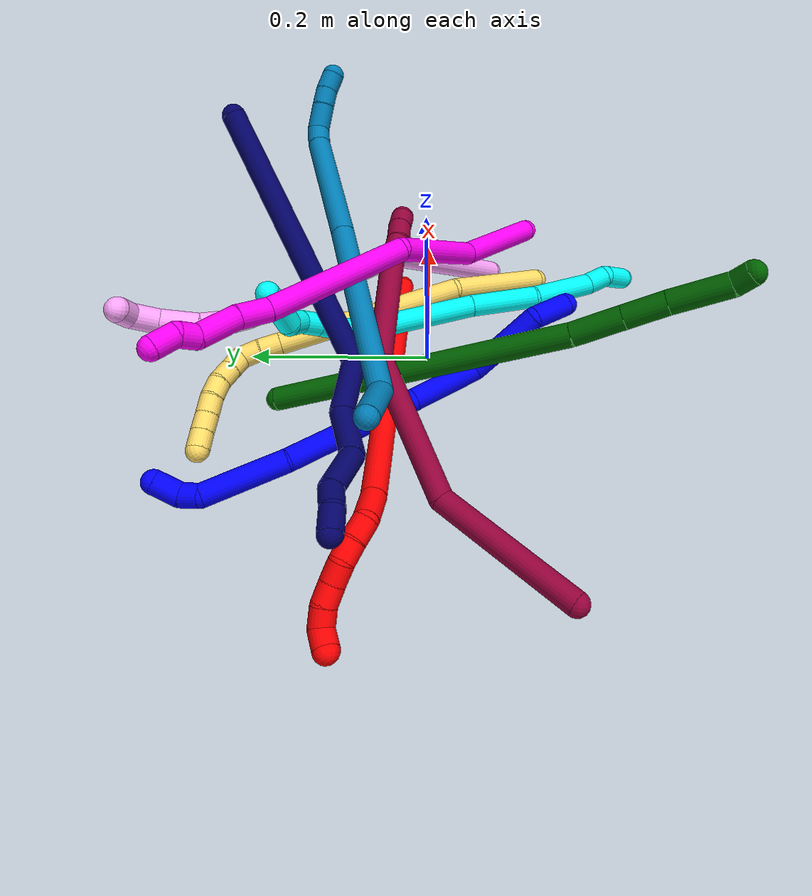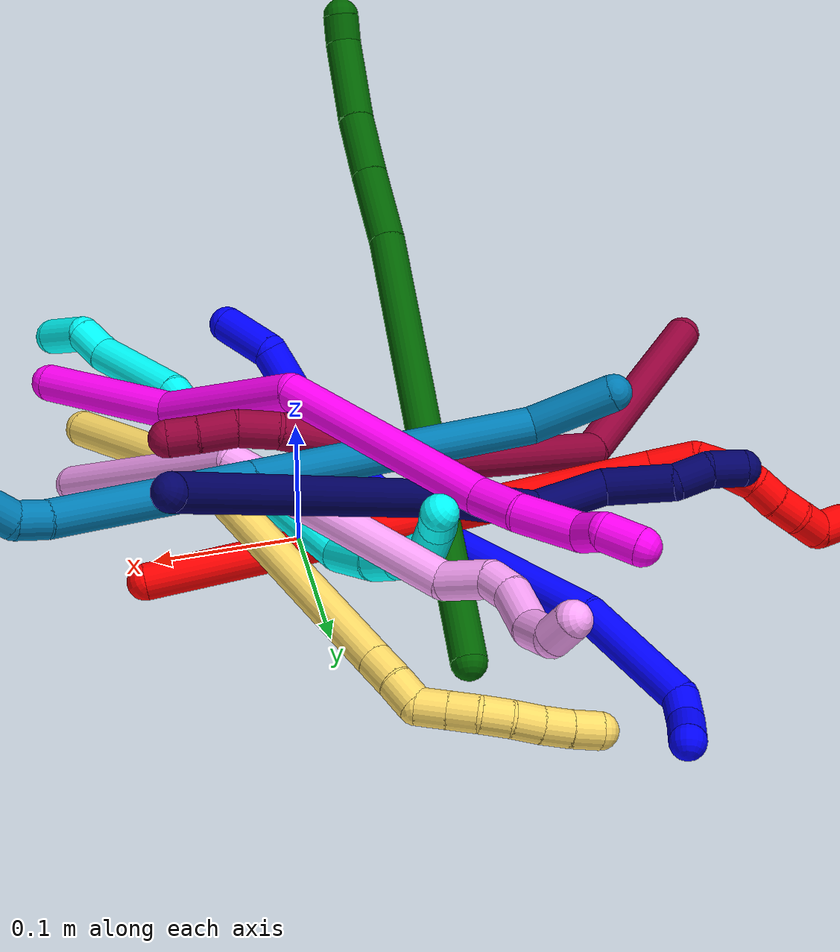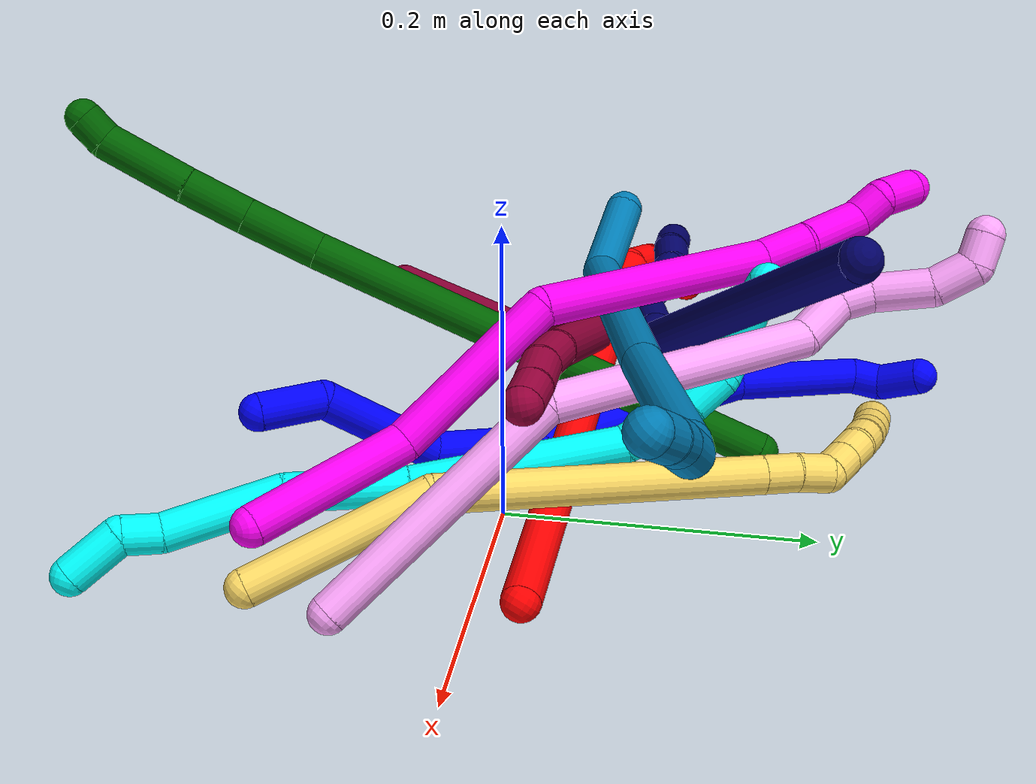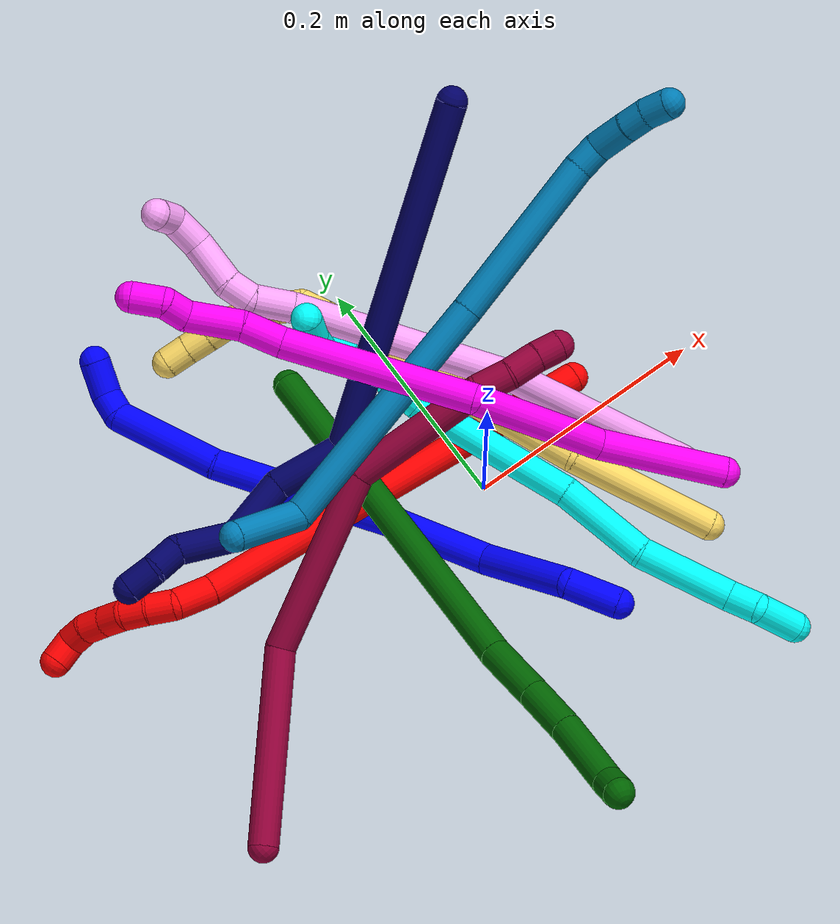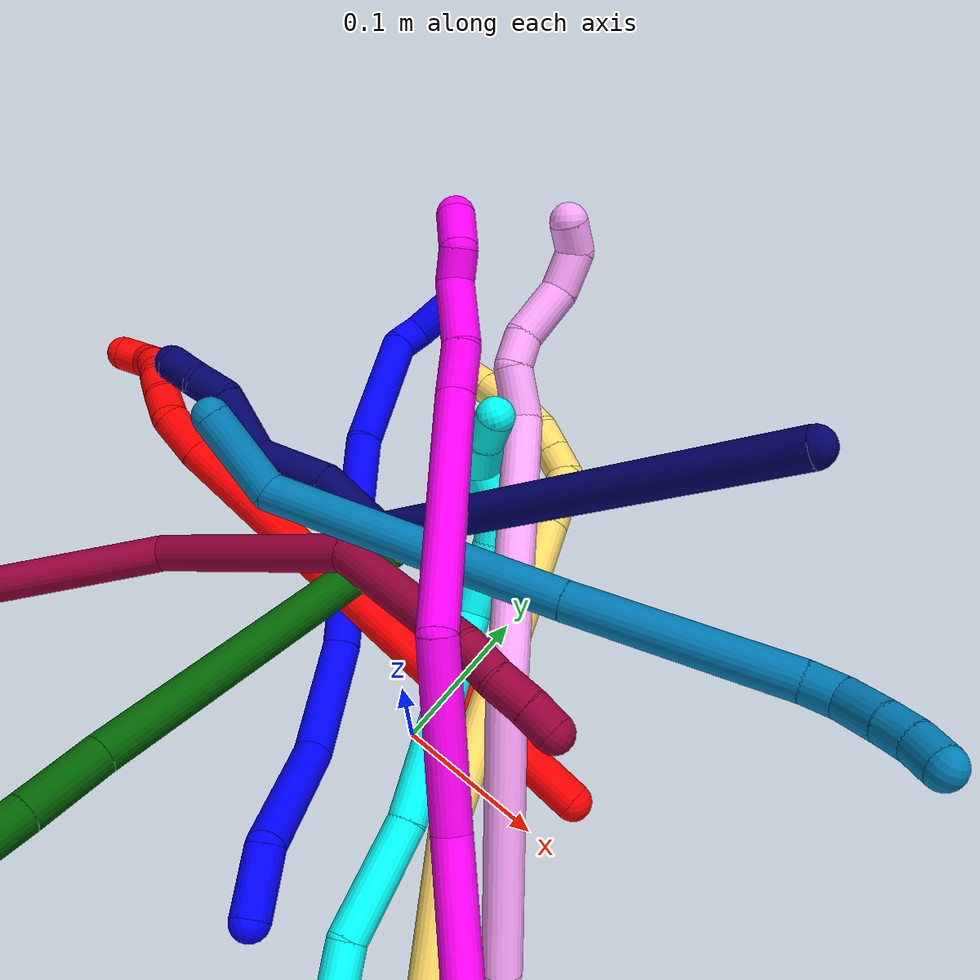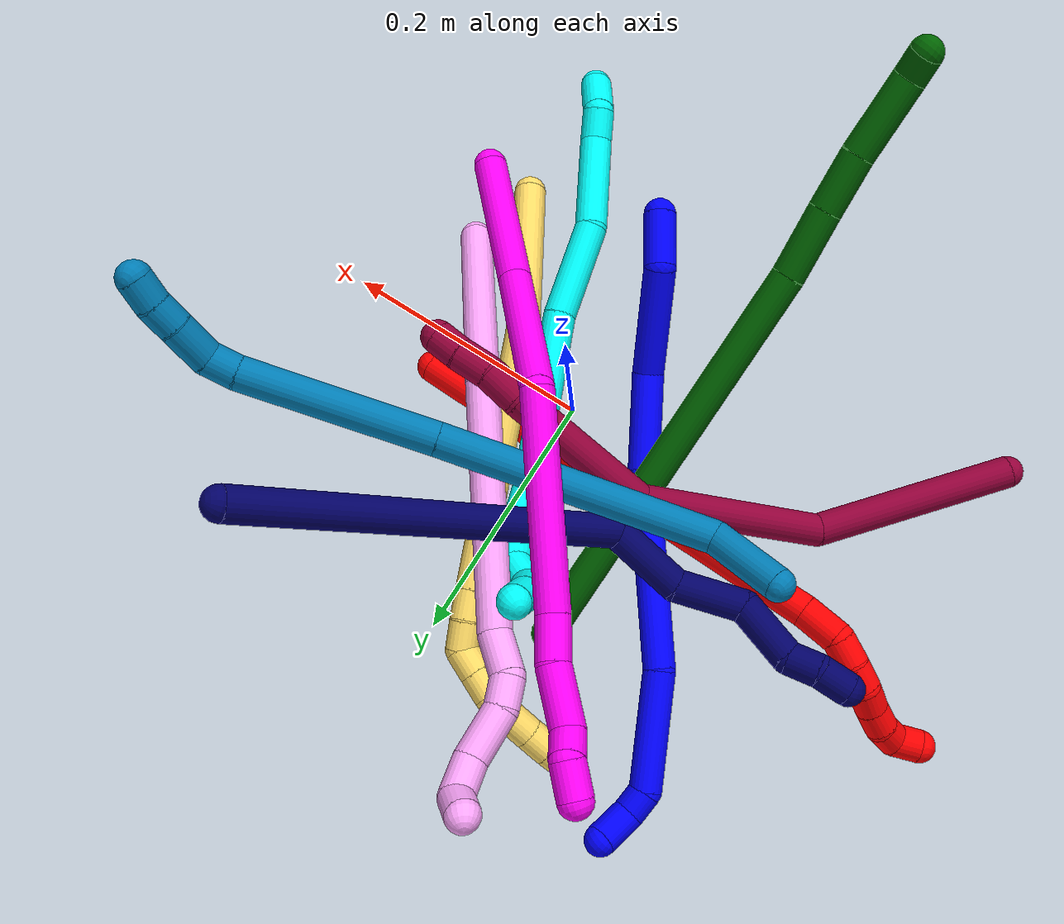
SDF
<sdf version="1.7">
 <world name="default">
  <plugin name="TubeGeneratorPlugin" filename="libtube_generator_plugin.so"/>
  <model name="photoneo_s_sensor">
   <static>1</static>
   <pose>0 0 2 1.57079 1.57079 3.14159</pose>
   <link name="link">
    <inertial><mass>0.1</mass></inertial>
    <sensor name="sensor" type="depth">
     <update_rate>30</update_rate>
     <camera>
      <horizontal_fov>1.22</horizontal_fov>
      <image><width>1920</width><height>1200</height><format>B8G8R8</format></image>
      <clip><near>0.1</near><far>4</far></clip>
      <depth_camera><output>points</output></depth_camera>
     </camera>
     <plugin name="camera_plugin" filename="libgazebo_ros_depth_camera.so">
      <baseline>0.2</baseline>
      <alwaysOn>1</alwaysOn>
      <updateRate>0.0</updateRate>
      <cameraName>camera_ir</cameraName>
      <imageTopicName>/camera/color/image_raw</imageTopicName>
      <cameraInfoTopicName>/camera/color/camera_info</cameraInfoTopicName>
      <depthImageTopicName>/camera/depth/image_raw</depthImageTopicName>
      <depthImageCameraInfoTopicName>/camera/depth/camera_info</depthImageCameraInfoTopicName>
      <pointCloudTopicName>/camera/depth/points</pointCloudTopicName>
      <frameName>fr_optical</frameName>
      <pointCloudCutoff>0.1</pointCloudCutoff>
      <pointCloudCutoffMax>2.0</pointCloudCutoffMax>
      <distortionK1>0</distortionK1>
      <distortionK2>0</distortionK2>
      <distortionK3>0</distortionK3>
      <distortionT1>0</distortionT1>
      <distortionT2>0</distortionT2>
      <CxPrime>0</CxPrime>
      <Cx>0</Cx>
      <Cy>0</Cy>
      <focalLength>0</focalLength>
      <hackBaseline>0</hackBaseline>
     </plugin>
    </sensor>
   </link>
  </model>
  <gravity>0 0 -9.8</gravity>
  <magnetic_field>6e-06 2.3e-05 -4.2e-05</magnetic_field>
  <atmosphere type="adiabatic"/>
  <physics name="default_physics" default="0" type="ode">
   <max_step_size>0.003</max_step_size>
   <real_time_factor>1</real_time_factor>
   <real_time_update_rate>1000</real_time_update_rate>
   <max_contacts>10000</max_contacts>
   <ode>
    <solver>
     <type>quick</type>
     <iters>100</iters>
     <sor>1.3</sor>
     <use_dynamic_moi_rescaling>0</use_dynamic_moi_rescaling>
    </solver>
    <constraints>
     <contact_max_correcting_vel>0</contact_max_correcting_vel>
     <contact_surface_layer>0.001</contact_surface_layer>
     <cfm>0</cfm>
     <erp>0.2</erp>
    </constraints>
   </ode>
  </physics>
  <scene><ambient>0.4 0.4 0.4 1</ambient><background>0.7 0.7 0.7 1</background><shadows>0</shadows></scene>
  <audio><device>default</device></audio>
  <spherical_coordinates>
   <surface_model>EARTH_WGS84</surface_model>
   <latitude_deg>0</latitude_deg>
   <longitude_deg>0</longitude_deg>
   <elevation>0</elevation>
   <heading_deg>0</heading_deg>
  </spherical_coordinates>
  <model name="bin">
   <static>1</static>
   <link name="bottom">
    <collision name="collision-bottom">
     <pose>0 0 -0.01 0 -0 0</pose>
     <geometry><box><size>0.8 0.6 0.02</size></box></geometry>
     <surface>
      <friction><ode><mu>100</mu><mu2>100</mu2></ode></friction>
      <contact><collide_bitmask>65535</collide_bitmask></contact>
     </surface>
    </collision>
   </link>
   <link name="west_wall">
    <collision name="collision-west_wall">
     <pose>-0.41 0 0.1 0 -0 0</pose>
     <geometry><box><size>0.02 0.6 0.2</size></box></geometry>
     <surface>
      <friction><ode><mu>100</mu><mu2>100</mu2></ode></friction>
      <contact><collide_bitmask>65535</collide_bitmask></contact>
     </surface>
    </collision>
   </link>
   <link name="east_wall">
    <collision name="collision-east_wall">
     <pose>0.41 0 0.1 0 -0 0</pose>
     <geometry><box><size>0.02 0.6 0.2</size></box></geometry>
     <surface>
      <friction><ode><mu>100</mu><mu2>100</mu2></ode></friction>
      <contact><collide_bitmask>65535</collide_bitmask></contact>
     </surface>
    </collision>
   </link>
   <link name="south_wall">
    <collision name="collision-south_wall">
     <pose>0 -0.31 0.1 0 -0 0</pose>
     <geometry><box><size>0.8 0.02 0.2</size></box></geometry>
     <surface>
      <friction><ode><mu>100</mu><mu2>100</mu2></ode></friction>
      <contact><collide_bitmask>65535</collide_bitmask></contact>
     </surface>
    </collision>
   </link>
   <link name="north_wall">
    <collision name="collision-north_wall">
     <pose>0 0.31 0.1 0 -0 0</pose>
     <geometry><box><size>0.8 0.02 0.2</size></box></geometry>
     <surface>
      <friction><ode><mu>100</mu><mu2>100</mu2></ode></friction>
      <contact><collide_bitmask>65535</collide_bitmask></contact>
     </surface>
    </collision>
   </link>
  </model>
  <model name="1">
   <static>0</static>
   <link name="1">
    <collision name="collision-cylinder-e_1_1_4">
     <pose>-0.011645 0.011863 0.013375 -0.725548 -0.577321 0.224484</pose>
     <geometry><cylinder><radius>0.0125</radius><length>0.042672</length></cylinder></geometry>
     <surface>
      <friction><ode><mu>1.16</mu><mu2>1.16</mu2><slip1>0</slip1><slip2>0</slip2></ode></friction>
      <contact><ode><kp>1e+06</kp><kd>1</kd><max_vel>0</max_vel><min_depth>0.001</min_depth></ode></contact>
     </surface>
    </collision>
    <visual name="visual-cylinder-e_1_1_4">
     <pose>-0.011645 0.011863 0.013375 -0.725548 -0.577321 0.224484</pose>
     <geometry><cylinder><radius>0.0125</radius><length>0.042672</length></cylinder></geometry>
     <material><ambient>0 0 1 1</ambient></material>
    </visual>
    <collision name="collision-cylinder-e_2_4_5">
     <pose>-0.021048 0.051606 0.059332 -0.707794 0.052234 -0.019302</pose>
     <geometry><cylinder><radius>0.0125</radius><length>0.085881</length></cylinder></geometry>
     <surface>
      <friction><ode><mu>1.16</mu><mu2>1.16</mu2><slip1>0</slip1><slip2>0</slip2></ode></friction>
      <contact><ode><kp>1e+06</kp><kd>1</kd><max_vel>0</max_vel><min_depth>0.001</min_depth></ode></contact>
     </surface>
    </collision>
    <visual name="visual-cylinder-e_2_4_5">
     <pose>-0.021048 0.051606 0.059332 -0.707794 0.052234 -0.019302</pose>
     <geometry><cylinder><radius>0.0125</radius><length>0.085881</length></cylinder></geometry>
     <material><ambient>0 0 1 1</ambient></material>
    </visual>
    <collision name="collision-cylinder-e_3_5_6">
     <pose>-0.035381 0.101931 0.1187 -0.697434 -0.44288 0.163341</pose>
     <geometry><cylinder><radius>0.0125</radius><length>0.077357</length></cylinder></geometry>
     <surface>
      <friction><ode><mu>1.16</mu><mu2>1.16</mu2><slip1>0</slip1><slip2>0</slip2></ode></friction>
      <contact><ode><kp>1e+06</kp><kd>1</kd><max_vel>0</max_vel><min_depth>0.001</min_depth></ode></contact>
     </surface>
    </collision>
    <visual name="visual-cylinder-e_3_5_6">
     <pose>-0.035381 0.101931 0.1187 -0.697434 -0.44288 0.163341</pose>
     <geometry><cylinder><radius>0.0125</radius><length>0.077357</length></cylinder></geometry>
     <material><ambient>0 0 1 1</ambient></material>
    </visual>
    <collision name="collision-cylinder-e_4_6_7">
     <pose>-0.097917 0.169243 0.188245 -0.809465 -0.638074 0.281141</pose>
     <geometry><cylinder><radius>0.0125</radius><length>0.154322</length></cylinder></geometry>
     <surface>
      <friction><ode><mu>1.16</mu><mu2>1.16</mu2><slip1>0</slip1><slip2>0</slip2></ode></friction>
      <contact><ode><kp>1e+06</kp><kd>1</kd><max_vel>0</max_vel><min_depth>0.001</min_depth></ode></contact>
     </surface>
    </collision>
    <visual name="visual-cylinder-e_4_6_7">
     <pose>-0.097917 0.169243 0.188245 -0.809465 -0.638074 0.281141</pose>
     <geometry><cylinder><radius>0.0125</radius><length>0.154322</length></cylinder></geometry>
     <material><ambient>0 0 1 1</ambient></material>
    </visual>
    <collision name="collision-cylinder-e_5_7_8">
     <pose>-0.164092 0.237007 0.263743 -0.61028 -0.468396 0.15001</pose>
     <geometry><cylinder><radius>0.0125</radius><length>0.089547</length></cylinder></geometry>
     <surface>
      <friction><ode><mu>1.16</mu><mu2>1.16</mu2><slip1>0</slip1><slip2>0</slip2></ode></friction>
      <contact><ode><kp>1e+06</kp><kd>1</kd><max_vel>0</max_vel><min_depth>0.001</min_depth></ode></contact>
     </surface>
    </collision>
    <visual name="visual-cylinder-e_5_7_8">
     <pose>-0.164092 0.237007 0.263743 -0.61028 -0.468396 0.15001</pose>
     <geometry><cylinder><radius>0.0125</radius><length>0.089547</length></cylinder></geometry>
     <material><ambient>0 0 1 1</ambient></material>
    </visual>
    <collision name="collision-cylinder-e_6_8_9">
     <pose>-0.186937 0.260551 0.306441 -0.064994 -0.257874 0.00843</pose>
     <geometry><cylinder><radius>0.0125</radius><length>0.020642</length></cylinder></geometry>
     <surface>
      <friction><ode><mu>1.16</mu><mu2>1.16</mu2><slip1>0</slip1><slip2>0</slip2></ode></friction>
      <contact><ode><kp>1e+06</kp><kd>1</kd><max_vel>0</max_vel><min_depth>0.001</min_depth></ode></contact>
     </surface>
    </collision>
    <visual name="visual-cylinder-e_6_8_9">
     <pose>-0.186937 0.260551 0.306441 -0.064994 -0.257874 0.00843</pose>
     <geometry><cylinder><radius>0.0125</radius><length>0.020642</length></cylinder></geometry>
     <material><ambient>0 0 1 1</ambient></material>
    </visual>
    <collision name="collision-cylinder-e_7_9_2">
     <pose>-0.198123 0.256778 0.327625 0.375228 -0.616757 -0.120801</pose>
     <geometry><cylinder><radius>0.0125</radius><length>0.029579</length></cylinder></geometry>
     <surface>
      <friction><ode><mu>1.16</mu><mu2>1.16</mu2><slip1>0</slip1><slip2>0</slip2></ode></friction>
      <contact><ode><kp>1e+06</kp><kd>1</kd><max_vel>0</max_vel><min_depth>0.001</min_depth></ode></contact>
     </surface>
    </collision>
    <visual name="visual-cylinder-e_7_9_2">
     <pose>-0.198123 0.256778 0.327625 0.375228 -0.616757 -0.120801</pose>
     <geometry><cylinder><radius>0.0125</radius><length>0.029579</length></cylinder></geometry>
     <material><ambient>0 0 1 1</ambient></material>
    </visual>
    <collision name="collision-sphere-2">
     <pose>-0.206677 0.252356 0.33885 0 -0 0</pose>
     <geometry><sphere><radius>0.0125</radius></sphere></geometry>
     <surface>
      <friction><ode><mu>1.16</mu><mu2>1.16</mu2><slip1>0</slip1><slip2>0</slip2></ode></friction>
      <contact><ode><kp>1e+06</kp><kd>1</kd><max_vel>0</max_vel><min_depth>0.001</min_depth></ode></contact>
     </surface>
    </collision>
    <visual name="visual-sphere-2">
     <pose>-0.206677 0.252356 0.33885 0 -0 0</pose>
     <geometry><sphere><radius>0.0125</radius></sphere></geometry>
     <material><ambient>0 0 1 1</ambient></material>
    </visual>
    <collision name="collision-sphere-9">
     <pose>-0.189569 0.261199 0.3164 0 -0 0</pose>
     <geometry><sphere><radius>0.0125</radius></sphere></geometry>
     <surface>
      <friction><ode><mu>1.16</mu><mu2>1.16</mu2><slip1>0</slip1><slip2>0</slip2></ode></friction>
      <contact><ode><kp>1e+06</kp><kd>1</kd><max_vel>0</max_vel><min_depth>0.001</min_depth></ode></contact>
     </surface>
    </collision>
    <visual name="visual-sphere-9">
     <pose>-0.189569 0.261199 0.3164 0 -0 0</pose>
     <geometry><sphere><radius>0.0125</radius></sphere></geometry>
     <material><ambient>0 0 1 1</ambient></material>
    </visual>
    <collision name="collision-sphere-4">
     <pose>-0.02329 0.023726 0.02675 0 -0 0</pose>
     <geometry><sphere><radius>0.0125</radius></sphere></geometry>
     <surface>
      <friction><ode><mu>1.16</mu><mu2>1.16</mu2><slip1>0</slip1><slip2>0</slip2></ode></friction>
      <contact><ode><kp>1e+06</kp><kd>1</kd><max_vel>0</max_vel><min_depth>0.001</min_depth></ode></contact>
     </surface>
    </collision>
    <visual name="visual-sphere-4">
     <pose>-0.02329 0.023726 0.02675 0 -0 0</pose>
     <geometry><sphere><radius>0.0125</radius></sphere></geometry>
     <material><ambient>0 0 1 1</ambient></material>
    </visual>
    <collision name="collision-sphere-1">
     <geometry><sphere><radius>0.0125</radius></sphere></geometry>
     <surface>
      <friction><ode><mu>1.16</mu><mu2>1.16</mu2><slip1>0</slip1><slip2>0</slip2></ode></friction>
      <contact><ode><kp>1e+06</kp><kd>1</kd><max_vel>0</max_vel><min_depth>0.001</min_depth></ode></contact>
     </surface>
    </collision>
    <visual name="visual-sphere-1">
     <geometry><sphere><radius>0.0125</radius></sphere></geometry>
     <material><ambient>0 0 1 1</ambient></material>
    </visual>
    <collision name="collision-sphere-8">
     <pose>-0.184305 0.259903 0.296483 0 -0 0</pose>
     <geometry><sphere><radius>0.0125</radius></sphere></geometry>
     <surface>
      <friction><ode><mu>1.16</mu><mu2>1.16</mu2><slip1>0</slip1><slip2>0</slip2></ode></friction>
      <contact><ode><kp>1e+06</kp><kd>1</kd><max_vel>0</max_vel><min_depth>0.001</min_depth></ode></contact>
     </surface>
    </collision>
    <visual name="visual-sphere-8">
     <pose>-0.184305 0.259903 0.296483 0 -0 0</pose>
     <geometry><sphere><radius>0.0125</radius></sphere></geometry>
     <material><ambient>0 0 1 1</ambient></material>
    </visual>
    <collision name="collision-sphere-5">
     <pose>-0.018806 0.079486 0.091914 0 -0 0</pose>
     <geometry><sphere><radius>0.0125</radius></sphere></geometry>
     <surface>
      <friction><ode><mu>1.16</mu><mu2>1.16</mu2><slip1>0</slip1><slip2>0</slip2></ode></friction>
      <contact><ode><kp>1e+06</kp><kd>1</kd><max_vel>0</max_vel><min_depth>0.001</min_depth></ode></contact>
     </surface>
    </collision>
    <visual name="visual-sphere-5">
     <pose>-0.018806 0.079486 0.091914 0 -0 0</pose>
     <geometry><sphere><radius>0.0125</radius></sphere></geometry>
     <material><ambient>0 0 1 1</ambient></material>
    </visual>
    <collision name="collision-sphere-6">
     <pose>-0.051956 0.124375 0.145487 0 -0 0</pose>
     <geometry><sphere><radius>0.0125</radius></sphere></geometry>
     <surface>
      <friction><ode><mu>1.16</mu><mu2>1.16</mu2><slip1>0</slip1><slip2>0</slip2></ode></friction>
      <contact><ode><kp>1e+06</kp><kd>1</kd><max_vel>0</max_vel><min_depth>0.001</min_depth></ode></contact>
     </surface>
    </collision>
    <visual name="visual-sphere-6">
     <pose>-0.051956 0.124375 0.145487 0 -0 0</pose>
     <geometry><sphere><radius>0.0125</radius></sphere></geometry>
     <material><ambient>0 0 1 1</ambient></material>
    </visual>
    <collision name="collision-sphere-7">
     <pose>-0.143878 0.214111 0.231004 0 -0 0</pose>
     <geometry><sphere><radius>0.0125</radius></sphere></geometry>
     <surface>
      <friction><ode><mu>1.16</mu><mu2>1.16</mu2><slip1>0</slip1><slip2>0</slip2></ode></friction>
      <contact><ode><kp>1e+06</kp><kd>1</kd><max_vel>0</max_vel><min_depth>0.001</min_depth></ode></contact>
     </surface>
    </collision>
    <visual name="visual-sphere-7">
     <pose>-0.143878 0.214111 0.231004 0 -0 0</pose>
     <geometry><sphere><radius>0.0125</radius></sphere></geometry>
     <material><ambient>0 0 1 1</ambient></material>
    </visual>
    <inertial>
     <pose>-0.08913 0.146276 0.167065 0 -0 0</pose>
     <mass>0.5</mass>
     <inertia>
      <ixx>0.000469</ixx>
      <ixy>0</ixy>
      <ixz>0</ixz>
      <iyy>0.000489</iyy>
      <iyz>0</iyz>
      <izz>-1.5e-05</izz>
     </inertia>
    </inertial>
   </link>
   <pose>0.016384 -0.153303 0.06956 -2.189 0.991979 -0.824628</pose>
  </model>
  <model name="2">
   <static>0</static>
   <link name="2">
    <collision name="collision-cylinder-e_1_1_4">
     <pose>-0.123266 -0.035645 0.116397 0.297173 -0.791657 -0.124943</pose>
     <geometry><cylinder><radius>0.0125</radius><length>0.346487</length></cylinder></geometry>
     <surface>
      <friction><ode><mu>1.16</mu><mu2>1.16</mu2><slip1>0</slip1><slip2>0</slip2></ode></friction>
      <contact><ode><kp>1e+06</kp><kd>1</kd><max_vel>0</max_vel><min_depth>0.001</min_depth></ode></contact>
     </surface>
    </collision>
    <visual name="visual-cylinder-e_1_1_4">
     <pose>-0.123266 -0.035645 0.116397 0.297173 -0.791657 -0.124943</pose>
     <geometry><cylinder><radius>0.0125</radius><length>0.346487</length></cylinder></geometry>
     <material><ambient>1 0 0 1</ambient></material>
    </visual>
    <collision name="collision-cylinder-e_2_4_5">
     <pose>-0.256221 -0.073365 0.244796 0.171127 -0.671963 -0.059889</pose>
     <geometry><cylinder><radius>0.0125</radius><length>0.031129</length></cylinder></geometry>
     <surface>
      <friction><ode><mu>1.16</mu><mu2>1.16</mu2><slip1>0</slip1><slip2>0</slip2></ode></friction>
      <contact><ode><kp>1e+06</kp><kd>1</kd><max_vel>0</max_vel><min_depth>0.001</min_depth></ode></contact>
     </surface>
    </collision>
    <visual name="visual-cylinder-e_2_4_5">
     <pose>-0.256221 -0.073365 0.244796 0.171127 -0.671963 -0.059889</pose>
     <geometry><cylinder><radius>0.0125</radius><length>0.031129</length></cylinder></geometry>
     <material><ambient>1 0 0 1</ambient></material>
    </visual>
    <collision name="collision-cylinder-e_3_5_6">
     <pose>-0.274285 -0.071926 0.263026 -0.513616 -0.86418 0.24103</pose>
     <geometry><cylinder><radius>0.0125</radius><length>0.022024</length></cylinder></geometry>
     <surface>
      <friction><ode><mu>1.16</mu><mu2>1.16</mu2><slip1>0</slip1><slip2>0</slip2></ode></friction>
      <contact><ode><kp>1e+06</kp><kd>1</kd><max_vel>0</max_vel><min_depth>0.001</min_depth></ode></contact>
     </surface>
    </collision>
    <visual name="visual-cylinder-e_3_5_6">
     <pose>-0.274285 -0.071926 0.263026 -0.513616 -0.86418 0.24103</pose>
     <geometry><cylinder><radius>0.0125</radius><length>0.022024</length></cylinder></geometry>
     <material><ambient>1 0 0 1</ambient></material>
    </visual>
    <collision name="collision-cylinder-e_4_6_7">
     <pose>-0.290949 -0.06452 0.273477 -0.744735 -0.964762 0.403492</pose>
     <geometry><cylinder><radius>0.0125</radius><length>0.020169</length></cylinder></geometry>
     <surface>
      <friction><ode><mu>1.16</mu><mu2>1.16</mu2><slip1>0</slip1><slip2>0</slip2></ode></friction>
      <contact><ode><kp>1e+06</kp><kd>1</kd><max_vel>0</max_vel><min_depth>0.001</min_depth></ode></contact>
     </surface>
    </collision>
    <visual name="visual-cylinder-e_4_6_7">
     <pose>-0.290949 -0.06452 0.273477 -0.744735 -0.964762 0.403492</pose>
     <geometry><cylinder><radius>0.0125</radius><length>0.020169</length></cylinder></geometry>
     <material><ambient>1 0 0 1</ambient></material>
    </visual>
    <collision name="collision-cylinder-e_5_7_8">
     <pose>-0.308015 -0.055886 0.278608 -1.38164 -1.06794 0.909305</pose>
     <geometry><cylinder><radius>0.0125</radius><length>0.020033</length></cylinder></geometry>
     <surface>
      <friction><ode><mu>1.16</mu><mu2>1.16</mu2><slip1>0</slip1><slip2>0</slip2></ode></friction>
      <contact><ode><kp>1e+06</kp><kd>1</kd><max_vel>0</max_vel><min_depth>0.001</min_depth></ode></contact>
     </surface>
    </collision>
    <visual name="visual-cylinder-e_5_7_8">
     <pose>-0.308015 -0.055886 0.278608 -1.38164 -1.06794 0.909305</pose>
     <geometry><cylinder><radius>0.0125</radius><length>0.020033</length></cylinder></geometry>
     <material><ambient>1 0 0 1</ambient></material>
    </visual>
    <collision name="collision-cylinder-e_6_8_9">
     <pose>-0.325872 -0.047205 0.281308 -1.14391 -1.12607 0.771871</pose>
     <geometry><cylinder><radius>0.0125</radius><length>0.02012</length></cylinder></geometry>
     <surface>
      <friction><ode><mu>1.16</mu><mu2>1.16</mu2><slip1>0</slip1><slip2>0</slip2></ode></friction>
      <contact><ode><kp>1e+06</kp><kd>1</kd><max_vel>0</max_vel><min_depth>0.001</min_depth></ode></contact>
     </surface>
    </collision>
    <visual name="visual-cylinder-e_6_8_9">
     <pose>-0.325872 -0.047205 0.281308 -1.14391 -1.12607 0.771871</pose>
     <geometry><cylinder><radius>0.0125</radius><length>0.02012</length></cylinder></geometry>
     <material><ambient>1 0 0 1</ambient></material>
    </visual>
    <collision name="collision-cylinder-e_7_9_10">
     <pose>-0.344728 -0.041143 0.282872 -1.67739 -1.35576 1.46111</pose>
     <geometry><cylinder><radius>0.0125</radius><length>0.020009</length></cylinder></geometry>
     <surface>
      <friction><ode><mu>1.16</mu><mu2>1.16</mu2><slip1>0</slip1><slip2>0</slip2></ode></friction>
      <contact><ode><kp>1e+06</kp><kd>1</kd><max_vel>0</max_vel><min_depth>0.001</min_depth></ode></contact>
     </surface>
    </collision>
    <visual name="visual-cylinder-e_7_9_10">
     <pose>-0.344728 -0.041143 0.282872 -1.67739 -1.35576 1.46111</pose>
     <geometry><cylinder><radius>0.0125</radius><length>0.020009</length></cylinder></geometry>
     <material><ambient>1 0 0 1</ambient></material>
    </visual>
    <collision name="collision-cylinder-e_8_10_2">
     <pose>-0.362788 -0.043323 0.286268 0.870982 -0.974504 -0.483434</pose>
     <geometry><cylinder><radius>0.0125</radius><length>0.02003</length></cylinder></geometry>
     <surface>
      <friction><ode><mu>1.16</mu><mu2>1.16</mu2><slip1>0</slip1><slip2>0</slip2></ode></friction>
      <contact><ode><kp>1e+06</kp><kd>1</kd><max_vel>0</max_vel><min_depth>0.001</min_depth></ode></contact>
     </surface>
    </collision>
    <visual name="visual-cylinder-e_8_10_2">
     <pose>-0.362788 -0.043323 0.286268 0.870982 -0.974504 -0.483434</pose>
     <geometry><cylinder><radius>0.0125</radius><length>0.02003</length></cylinder></geometry>
     <material><ambient>1 0 0 1</ambient></material>
    </visual>
    <collision name="collision-sphere-2">
     <pose>-0.371075 -0.047625 0.28989 0 -0 0</pose>
     <geometry><sphere><radius>0.0125</radius></sphere></geometry>
     <surface>
      <friction><ode><mu>1.16</mu><mu2>1.16</mu2><slip1>0</slip1><slip2>0</slip2></ode></friction>
      <contact><ode><kp>1e+06</kp><kd>1</kd><max_vel>0</max_vel><min_depth>0.001</min_depth></ode></contact>
     </surface>
    </collision>
    <visual name="visual-sphere-2">
     <pose>-0.371075 -0.047625 0.28989 0 -0 0</pose>
     <geometry><sphere><radius>0.0125</radius></sphere></geometry>
     <material><ambient>1 0 0 1</ambient></material>
    </visual>
    <collision name="collision-sphere-10">
     <pose>-0.354501 -0.039021 0.282645 0 -0 0</pose>
     <geometry><sphere><radius>0.0125</radius></sphere></geometry>
     <surface>
      <friction><ode><mu>1.16</mu><mu2>1.16</mu2><slip1>0</slip1><slip2>0</slip2></ode></friction>
      <contact><ode><kp>1e+06</kp><kd>1</kd><max_vel>0</max_vel><min_depth>0.001</min_depth></ode></contact>
     </surface>
    </collision>
    <visual name="visual-sphere-10">
     <pose>-0.354501 -0.039021 0.282645 0 -0 0</pose>
     <geometry><sphere><radius>0.0125</radius></sphere></geometry>
     <material><ambient>1 0 0 1</ambient></material>
    </visual>
    <collision name="collision-sphere-9">
     <pose>-0.334954 -0.043266 0.283099 0 -0 0</pose>
     <geometry><sphere><radius>0.0125</radius></sphere></geometry>
     <surface>
      <friction><ode><mu>1.16</mu><mu2>1.16</mu2><slip1>0</slip1><slip2>0</slip2></ode></friction>
      <contact><ode><kp>1e+06</kp><kd>1</kd><max_vel>0</max_vel><min_depth>0.001</min_depth></ode></contact>
     </surface>
    </collision>
    <visual name="visual-sphere-9">
     <pose>-0.334954 -0.043266 0.283099 0 -0 0</pose>
     <geometry><sphere><radius>0.0125</radius></sphere></geometry>
     <material><ambient>1 0 0 1</ambient></material>
    </visual>
    <collision name="collision-sphere-4">
     <pose>-0.246532 -0.071291 0.232793 0 -0 0</pose>
     <geometry><sphere><radius>0.0125</radius></sphere></geometry>
     <surface>
      <friction><ode><mu>1.16</mu><mu2>1.16</mu2><slip1>0</slip1><slip2>0</slip2></ode></friction>
      <contact><ode><kp>1e+06</kp><kd>1</kd><max_vel>0</max_vel><min_depth>0.001</min_depth></ode></contact>
     </surface>
    </collision>
    <visual name="visual-sphere-4">
     <pose>-0.246532 -0.071291 0.232793 0 -0 0</pose>
     <geometry><sphere><radius>0.0125</radius></sphere></geometry>
     <material><ambient>1 0 0 1</ambient></material>
    </visual>
    <collision name="collision-sphere-1">
     <geometry><sphere><radius>0.0125</radius></sphere></geometry>
     <surface>
      <friction><ode><mu>1.16</mu><mu2>1.16</mu2><slip1>0</slip1><slip2>0</slip2></ode></friction>
      <contact><ode><kp>1e+06</kp><kd>1</kd><max_vel>0</max_vel><min_depth>0.001</min_depth></ode></contact>
     </surface>
    </collision>
    <visual name="visual-sphere-1">
     <geometry><sphere><radius>0.0125</radius></sphere></geometry>
     <material><ambient>1 0 0 1</ambient></material>
    </visual>
    <collision name="collision-sphere-8">
     <pose>-0.316791 -0.051145 0.279516 0 -0 0</pose>
     <geometry><sphere><radius>0.0125</radius></sphere></geometry>
     <surface>
      <friction><ode><mu>1.16</mu><mu2>1.16</mu2><slip1>0</slip1><slip2>0</slip2></ode></friction>
      <contact><ode><kp>1e+06</kp><kd>1</kd><max_vel>0</max_vel><min_depth>0.001</min_depth></ode></contact>
     </surface>
    </collision>
    <visual name="visual-sphere-8">
     <pose>-0.316791 -0.051145 0.279516 0 -0 0</pose>
     <geometry><sphere><radius>0.0125</radius></sphere></geometry>
     <material><ambient>1 0 0 1</ambient></material>
    </visual>
    <collision name="collision-sphere-5">
     <pose>-0.26591 -0.075439 0.256799 0 -0 0</pose>
     <geometry><sphere><radius>0.0125</radius></sphere></geometry>
     <surface>
      <friction><ode><mu>1.16</mu><mu2>1.16</mu2><slip1>0</slip1><slip2>0</slip2></ode></friction>
      <contact><ode><kp>1e+06</kp><kd>1</kd><max_vel>0</max_vel><min_depth>0.001</min_depth></ode></contact>
     </surface>
    </collision>
    <visual name="visual-sphere-5">
     <pose>-0.26591 -0.075439 0.256799 0 -0 0</pose>
     <geometry><sphere><radius>0.0125</radius></sphere></geometry>
     <material><ambient>1 0 0 1</ambient></material>
    </visual>
    <collision name="collision-sphere-6">
     <pose>-0.282661 -0.068414 0.269253 0 -0 0</pose>
     <geometry><sphere><radius>0.0125</radius></sphere></geometry>
     <surface>
      <friction><ode><mu>1.16</mu><mu2>1.16</mu2><slip1>0</slip1><slip2>0</slip2></ode></friction>
      <contact><ode><kp>1e+06</kp><kd>1</kd><max_vel>0</max_vel><min_depth>0.001</min_depth></ode></contact>
     </surface>
    </collision>
    <visual name="visual-sphere-6">
     <pose>-0.282661 -0.068414 0.269253 0 -0 0</pose>
     <geometry><sphere><radius>0.0125</radius></sphere></geometry>
     <material><ambient>1 0 0 1</ambient></material>
    </visual>
    <collision name="collision-sphere-7">
     <pose>-0.299238 -0.060627 0.2777 0 -0 0</pose>
     <geometry><sphere><radius>0.0125</radius></sphere></geometry>
     <surface>
      <friction><ode><mu>1.16</mu><mu2>1.16</mu2><slip1>0</slip1><slip2>0</slip2></ode></friction>
      <contact><ode><kp>1e+06</kp><kd>1</kd><max_vel>0</max_vel><min_depth>0.001</min_depth></ode></contact>
     </surface>
    </collision>
    <visual name="visual-sphere-7">
     <pose>-0.299238 -0.060627 0.2777 0 -0 0</pose>
     <geometry><sphere><radius>0.0125</radius></sphere></geometry>
     <material><ambient>1 0 0 1</ambient></material>
    </visual>
    <inertial>
     <pose>-0.178972 -0.04256 0.163788 0 -0 0</pose>
     <mass>0.5</mass>
     <inertia><ixx>0.0021</ixx><ixy>0</ixy><ixz>0</ixz><iyy>0.003096</iyy><iyz>0</iyz><izz>0.003223</izz></inertia>
    </inertial>
   </link>
   <pose>0.11085 0.030544 0.011756 -0.511789 -0.639834 0.106286</pose>
  </model>
  <model name="3">
   <static>0</static>
   <link name="3">
    <collision name="collision-cylinder-e_1_1_4">
     <pose>-0.006565 0.005993 -0.016385 -2.79097 -0.359916 1.5975</pose>
     <geometry><cylinder><radius>0.0125</radius><length>0.037282</length></cylinder></geometry>
     <surface>
      <friction><ode><mu>1.16</mu><mu2>1.16</mu2><slip1>0</slip1><slip2>0</slip2></ode></friction>
      <contact><ode><kp>1e+06</kp><kd>1</kd><max_vel>0</max_vel><min_depth>0.001</min_depth></ode></contact>
     </surface>
    </collision>
    <visual name="visual-cylinder-e_1_1_4">
     <pose>-0.006565 0.005993 -0.016385 -2.79097 -0.359916 1.5975</pose>
     <geometry><cylinder><radius>0.0125</radius><length>0.037282</length></cylinder></geometry>
     <material><ambient>0.003922 1 0.996078 1</ambient></material>
    </visual>
    <collision name="collision-cylinder-e_2_4_5">
     <pose>-0.017723 0.022373 -0.038076 -2.04301 -0.375073 0.60123</pose>
     <geometry><cylinder><radius>0.0125</radius><length>0.025071</length></cylinder></geometry>
     <surface>
      <friction><ode><mu>1.16</mu><mu2>1.16</mu2><slip1>0</slip1><slip2>0</slip2></ode></friction>
      <contact><ode><kp>1e+06</kp><kd>1</kd><max_vel>0</max_vel><min_depth>0.001</min_depth></ode></contact>
     </surface>
    </collision>
    <visual name="visual-cylinder-e_2_4_5">
     <pose>-0.017723 0.022373 -0.038076 -2.04301 -0.375073 0.60123</pose>
     <geometry><cylinder><radius>0.0125</radius><length>0.025071</length></cylinder></geometry>
     <material><ambient>0.003922 1 0.996078 1</ambient></material>
    </visual>
    <collision name="collision-cylinder-e_3_5_6">
     <pose>-0.038029 0.057777 -0.068679 -2.36178 -0.415912 0.948729</pose>
     <geometry><cylinder><radius>0.0125</radius><length>0.077788</length></cylinder></geometry>
     <surface>
      <friction><ode><mu>1.16</mu><mu2>1.16</mu2><slip1>0</slip1><slip2>0</slip2></ode></friction>
      <contact><ode><kp>1e+06</kp><kd>1</kd><max_vel>0</max_vel><min_depth>0.001</min_depth></ode></contact>
     </surface>
    </collision>
    <visual name="visual-cylinder-e_3_5_6">
     <pose>-0.038029 0.057777 -0.068679 -2.36178 -0.415912 0.948729</pose>
     <geometry><cylinder><radius>0.0125</radius><length>0.077788</length></cylinder></geometry>
     <material><ambient>0.003922 1 0.996078 1</ambient></material>
    </visual>
    <collision name="collision-cylinder-e_4_6_7">
     <pose>-0.076836 0.108616 -0.110086 -2.12857 -0.649076 1.09025</pose>
     <geometry><cylinder><radius>0.0125</radius><length>0.076408</length></cylinder></geometry>
     <surface>
      <friction><ode><mu>1.16</mu><mu2>1.16</mu2><slip1>0</slip1><slip2>0</slip2></ode></friction>
      <contact><ode><kp>1e+06</kp><kd>1</kd><max_vel>0</max_vel><min_depth>0.001</min_depth></ode></contact>
     </surface>
    </collision>
    <visual name="visual-cylinder-e_4_6_7">
     <pose>-0.076836 0.108616 -0.110086 -2.12857 -0.649076 1.09025</pose>
     <geometry><cylinder><radius>0.0125</radius><length>0.076408</length></cylinder></geometry>
     <material><ambient>0.003922 1 0.996078 1</ambient></material>
    </visual>
    <collision name="collision-cylinder-e_5_7_8">
     <pose>-0.133148 0.181939 -0.163761 -2.23992 -0.501727 0.97374</pose>
     <geometry><cylinder><radius>0.0125</radius><length>0.138147</length></cylinder></geometry>
     <surface>
      <friction><ode><mu>1.16</mu><mu2>1.16</mu2><slip1>0</slip1><slip2>0</slip2></ode></friction>
      <contact><ode><kp>1e+06</kp><kd>1</kd><max_vel>0</max_vel><min_depth>0.001</min_depth></ode></contact>
     </surface>
    </collision>
    <visual name="visual-cylinder-e_5_7_8">
     <pose>-0.133148 0.181939 -0.163761 -2.23992 -0.501727 0.97374</pose>
     <geometry><cylinder><radius>0.0125</radius><length>0.138147</length></cylinder></geometry>
     <material><ambient>0.003922 1 0.996078 1</ambient></material>
    </visual>
    <collision name="collision-cylinder-e_6_8_9">
     <pose>-0.179841 0.236913 -0.219996 -2.76085 -0.590294 2.01173</pose>
     <geometry><cylinder><radius>0.0125</radius><length>0.04841</length></cylinder></geometry>
     <surface>
      <friction><ode><mu>1.16</mu><mu2>1.16</mu2><slip1>0</slip1><slip2>0</slip2></ode></friction>
      <contact><ode><kp>1e+06</kp><kd>1</kd><max_vel>0</max_vel><min_depth>0.001</min_depth></ode></contact>
     </surface>
    </collision>
    <visual name="visual-cylinder-e_6_8_9">
     <pose>-0.179841 0.236913 -0.219996 -2.76085 -0.590294 2.01173</pose>
     <geometry><cylinder><radius>0.0125</radius><length>0.04841</length></cylinder></geometry>
     <material><ambient>0.003922 1 0.996078 1</ambient></material>
    </visual>
    <collision name="collision-cylinder-e_7_9_10">
     <pose>-0.198229 0.247604 -0.249757 -2.85924 -0.402355 1.92432</pose>
     <geometry><cylinder><radius>0.0125</radius><length>0.025104</length></cylinder></geometry>
     <surface>
      <friction><ode><mu>1.16</mu><mu2>1.16</mu2><slip1>0</slip1><slip2>0</slip2></ode></friction>
      <contact><ode><kp>1e+06</kp><kd>1</kd><max_vel>0</max_vel><min_depth>0.001</min_depth></ode></contact>
     </surface>
    </collision>
    <visual name="visual-cylinder-e_7_9_10">
     <pose>-0.198229 0.247604 -0.249757 -2.85924 -0.402355 1.92432</pose>
     <geometry><cylinder><radius>0.0125</radius><length>0.025104</length></cylinder></geometry>
     <material><ambient>0.003922 1 0.996078 1</ambient></material>
    </visual>
    <collision name="collision-cylinder-e_8_10_11">
     <pose>-0.202231 0.253259 -0.272748 -2.9396 0.075047 -0.709535</pose>
     <geometry><cylinder><radius>0.0125</radius><length>0.024361</length></cylinder></geometry>
     <surface>
      <friction><ode><mu>1.16</mu><mu2>1.16</mu2><slip1>0</slip1><slip2>0</slip2></ode></friction>
      <contact><ode><kp>1e+06</kp><kd>1</kd><max_vel>0</max_vel><min_depth>0.001</min_depth></ode></contact>
     </surface>
    </collision>
    <visual name="visual-cylinder-e_8_10_11">
     <pose>-0.202231 0.253259 -0.272748 -2.9396 0.075047 -0.709535</pose>
     <geometry><cylinder><radius>0.0125</radius><length>0.024361</length></cylinder></geometry>
     <material><ambient>0.003922 1 0.996078 1</ambient></material>
    </visual>
    <collision name="collision-cylinder-e_9_11_12">
     <pose>-0.206082 0.250977 -0.295671 2.73711 -0.378209 -1.50195</pose>
     <geometry><cylinder><radius>0.0125</radius><length>0.025804</length></cylinder></geometry>
     <surface>
      <friction><ode><mu>1.16</mu><mu2>1.16</mu2><slip1>0</slip1><slip2>0</slip2></ode></friction>
      <contact><ode><kp>1e+06</kp><kd>1</kd><max_vel>0</max_vel><min_depth>0.001</min_depth></ode></contact>
     </surface>
    </collision>
    <visual name="visual-cylinder-e_9_11_12">
     <pose>-0.206082 0.250977 -0.295671 2.73711 -0.378209 -1.50195</pose>
     <geometry><cylinder><radius>0.0125</radius><length>0.025804</length></cylinder></geometry>
     <material><ambient>0.003922 1 0.996078 1</ambient></material>
    </visual>
    <collision name="collision-cylinder-e_10_12_2">
     <pose>-0.21702 0.242425 -0.3147 2.69514 -0.607684 -1.88829</pose>
     <geometry><cylinder><radius>0.0125</radius><length>0.021625</length></cylinder></geometry>
     <surface>
      <friction><ode><mu>1.16</mu><mu2>1.16</mu2><slip1>0</slip1><slip2>0</slip2></ode></friction>
      <contact><ode><kp>1e+06</kp><kd>1</kd><max_vel>0</max_vel><min_depth>0.001</min_depth></ode></contact>
     </surface>
    </collision>
    <visual name="visual-cylinder-e_10_12_2">
     <pose>-0.21702 0.242425 -0.3147 2.69514 -0.607684 -1.88829</pose>
     <geometry><cylinder><radius>0.0125</radius><length>0.021625</length></cylinder></geometry>
     <material><ambient>0.003922 1 0.996078 1</ambient></material>
    </visual>
    <collision name="collision-sphere-2">
     <pose>-0.223193 0.238593 -0.322706 0 -0 0</pose>
     <geometry><sphere><radius>0.0125</radius></sphere></geometry>
     <surface>
      <friction><ode><mu>1.16</mu><mu2>1.16</mu2><slip1>0</slip1><slip2>0</slip2></ode></friction>
      <contact><ode><kp>1e+06</kp><kd>1</kd><max_vel>0</max_vel><min_depth>0.001</min_depth></ode></contact>
     </surface>
    </collision>
    <visual name="visual-sphere-2">
     <pose>-0.223193 0.238593 -0.322706 0 -0 0</pose>
     <geometry><sphere><radius>0.0125</radius></sphere></geometry>
     <material><ambient>0.003922 1 0.996078 1</ambient></material>
    </visual>
    <collision name="collision-sphere-12">
     <pose>-0.210846 0.246258 -0.306693 0 -0 0</pose>
     <geometry><sphere><radius>0.0125</radius></sphere></geometry>
     <surface>
      <friction><ode><mu>1.16</mu><mu2>1.16</mu2><slip1>0</slip1><slip2>0</slip2></ode></friction>
      <contact><ode><kp>1e+06</kp><kd>1</kd><max_vel>0</max_vel><min_depth>0.001</min_depth></ode></contact>
     </surface>
    </collision>
    <visual name="visual-sphere-12">
     <pose>-0.210846 0.246258 -0.306693 0 -0 0</pose>
     <geometry><sphere><radius>0.0125</radius></sphere></geometry>
     <material><ambient>0.003922 1 0.996078 1</ambient></material>
    </visual>
    <collision name="collision-sphere-11">
     <pose>-0.201318 0.255695 -0.284648 0 -0 0</pose>
     <geometry><sphere><radius>0.0125</radius></sphere></geometry>
     <surface>
      <friction><ode><mu>1.16</mu><mu2>1.16</mu2><slip1>0</slip1><slip2>0</slip2></ode></friction>
      <contact><ode><kp>1e+06</kp><kd>1</kd><max_vel>0</max_vel><min_depth>0.001</min_depth></ode></contact>
     </surface>
    </collision>
    <visual name="visual-sphere-11">
     <pose>-0.201318 0.255695 -0.284648 0 -0 0</pose>
     <geometry><sphere><radius>0.0125</radius></sphere></geometry>
     <material><ambient>0.003922 1 0.996078 1</ambient></material>
    </visual>
    <collision name="collision-sphere-10">
     <pose>-0.203144 0.250822 -0.260849 0 -0 0</pose>
     <geometry><sphere><radius>0.0125</radius></sphere></geometry>
     <surface>
      <friction><ode><mu>1.16</mu><mu2>1.16</mu2><slip1>0</slip1><slip2>0</slip2></ode></friction>
      <contact><ode><kp>1e+06</kp><kd>1</kd><max_vel>0</max_vel><min_depth>0.001</min_depth></ode></contact>
     </surface>
    </collision>
    <visual name="visual-sphere-10">
     <pose>-0.203144 0.250822 -0.260849 0 -0 0</pose>
     <geometry><sphere><radius>0.0125</radius></sphere></geometry>
     <material><ambient>0.003922 1 0.996078 1</ambient></material>
    </visual>
    <collision name="collision-sphere-9">
     <pose>-0.193314 0.244386 -0.238664 0 -0 0</pose>
     <geometry><sphere><radius>0.0125</radius></sphere></geometry>
     <surface>
      <friction><ode><mu>1.16</mu><mu2>1.16</mu2><slip1>0</slip1><slip2>0</slip2></ode></friction>
      <contact><ode><kp>1e+06</kp><kd>1</kd><max_vel>0</max_vel><min_depth>0.001</min_depth></ode></contact>
     </surface>
    </collision>
    <visual name="visual-sphere-9">
     <pose>-0.193314 0.244386 -0.238664 0 -0 0</pose>
     <geometry><sphere><radius>0.0125</radius></sphere></geometry>
     <material><ambient>0.003922 1 0.996078 1</ambient></material>
    </visual>
    <collision name="collision-sphere-4">
     <pose>-0.013131 0.011985 -0.03277 0 -0 0</pose>
     <geometry><sphere><radius>0.0125</radius></sphere></geometry>
     <surface>
      <friction><ode><mu>1.16</mu><mu2>1.16</mu2><slip1>0</slip1><slip2>0</slip2></ode></friction>
      <contact><ode><kp>1e+06</kp><kd>1</kd><max_vel>0</max_vel><min_depth>0.001</min_depth></ode></contact>
     </surface>
    </collision>
    <visual name="visual-sphere-4">
     <pose>-0.013131 0.011985 -0.03277 0 -0 0</pose>
     <geometry><sphere><radius>0.0125</radius></sphere></geometry>
     <material><ambient>0.003922 1 0.996078 1</ambient></material>
    </visual>
    <collision name="collision-sphere-1">
     <geometry><sphere><radius>0.0125</radius></sphere></geometry>
     <surface>
      <friction><ode><mu>1.16</mu><mu2>1.16</mu2><slip1>0</slip1><slip2>0</slip2></ode></friction>
      <contact><ode><kp>1e+06</kp><kd>1</kd><max_vel>0</max_vel><min_depth>0.001</min_depth></ode></contact>
     </surface>
    </collision>
    <visual name="visual-sphere-1">
     <geometry><sphere><radius>0.0125</radius></sphere></geometry>
     <material><ambient>0.003922 1 0.996078 1</ambient></material>
    </visual>
    <collision name="collision-sphere-8">
     <pose>-0.166369 0.229441 -0.201327 0 -0 0</pose>
     <geometry><sphere><radius>0.0125</radius></sphere></geometry>
     <surface>
      <friction><ode><mu>1.16</mu><mu2>1.16</mu2><slip1>0</slip1><slip2>0</slip2></ode></friction>
      <contact><ode><kp>1e+06</kp><kd>1</kd><max_vel>0</max_vel><min_depth>0.001</min_depth></ode></contact>
     </surface>
    </collision>
    <visual name="visual-sphere-8">
     <pose>-0.166369 0.229441 -0.201327 0 -0 0</pose>
     <geometry><sphere><radius>0.0125</radius></sphere></geometry>
     <material><ambient>0.003922 1 0.996078 1</ambient></material>
    </visual>
    <collision name="collision-sphere-5">
     <pose>-0.022315 0.032761 -0.043381 0 -0 0</pose>
     <geometry><sphere><radius>0.0125</radius></sphere></geometry>
     <surface>
      <friction><ode><mu>1.16</mu><mu2>1.16</mu2><slip1>0</slip1><slip2>0</slip2></ode></friction>
      <contact><ode><kp>1e+06</kp><kd>1</kd><max_vel>0</max_vel><min_depth>0.001</min_depth></ode></contact>
     </surface>
    </collision>
    <visual name="visual-sphere-5">
     <pose>-0.022315 0.032761 -0.043381 0 -0 0</pose>
     <geometry><sphere><radius>0.0125</radius></sphere></geometry>
     <material><ambient>0.003922 1 0.996078 1</ambient></material>
    </visual>
    <collision name="collision-sphere-6">
     <pose>-0.053743 0.082794 -0.093977 0 -0 0</pose>
     <geometry><sphere><radius>0.0125</radius></sphere></geometry>
     <surface>
      <friction><ode><mu>1.16</mu><mu2>1.16</mu2><slip1>0</slip1><slip2>0</slip2></ode></friction>
      <contact><ode><kp>1e+06</kp><kd>1</kd><max_vel>0</max_vel><min_depth>0.001</min_depth></ode></contact>
     </surface>
    </collision>
    <visual name="visual-sphere-6">
     <pose>-0.053743 0.082794 -0.093977 0 -0 0</pose>
     <geometry><sphere><radius>0.0125</radius></sphere></geometry>
     <material><ambient>0.003922 1 0.996078 1</ambient></material>
    </visual>
    <collision name="collision-sphere-7">
     <pose>-0.099928 0.134438 -0.126195 0 -0 0</pose>
     <geometry><sphere><radius>0.0125</radius></sphere></geometry>
     <surface>
      <friction><ode><mu>1.16</mu><mu2>1.16</mu2><slip1>0</slip1><slip2>0</slip2></ode></friction>
      <contact><ode><kp>1e+06</kp><kd>1</kd><max_vel>0</max_vel><min_depth>0.001</min_depth></ode></contact>
     </surface>
    </collision>
    <visual name="visual-sphere-7">
     <pose>-0.099928 0.134438 -0.126195 0 -0 0</pose>
     <geometry><sphere><radius>0.0125</radius></sphere></geometry>
     <material><ambient>0.003922 1 0.996078 1</ambient></material>
    </visual>
    <inertial>
     <pose>-0.113064 0.148571 -0.151883 0 -0 0</pose>
     <mass>0.5</mass>
     <inertia><ixx>0.000364</ixx><ixy>0</ixy><ixz>0</ixz><iyy>0.000254</iyy><iyz>0</iyz><izz>-8e-05</izz></inertia>
    </inertial>
   </link>
   <pose>0.129118 -0.239491 0.011499 -2.42443 0.243796 -2.23716</pose>
  </model>
  <model name="4">
   <static>0</static>
   <link name="4">
    <collision name="collision-cylinder-e_1_1_4">
     <pose>0.000339 0.007073 0.087596 -0.080574 0.003856 -0.000155</pose>
     <geometry><cylinder><radius>0.0125</radius><length>0.175764</length></cylinder></geometry>
     <surface>
      <friction><ode><mu>1.16</mu><mu2>1.16</mu2><slip1>0</slip1><slip2>0</slip2></ode></friction>
      <contact><ode><kp>1e+06</kp><kd>1</kd><max_vel>0</max_vel><min_depth>0.001</min_depth></ode></contact>
     </surface>
    </collision>
    <visual name="visual-cylinder-e_1_1_4">
     <pose>0.000339 0.007073 0.087596 -0.080574 0.003856 -0.000155</pose>
     <geometry><cylinder><radius>0.0125</radius><length>0.175764</length></cylinder></geometry>
     <material><ambient>1 0.65098 0.996078 1</ambient></material>
    </visual>
    <collision name="collision-cylinder-e_2_4_5">
     <pose>-0.030507 0.057667 0.247277 -0.543161 -0.354693 0.099734</pose>
     <geometry><cylinder><radius>0.0125</radius><length>0.179585</length></cylinder></geometry>
     <surface>
      <friction><ode><mu>1.16</mu><mu2>1.16</mu2><slip1>0</slip1><slip2>0</slip2></ode></friction>
      <contact><ode><kp>1e+06</kp><kd>1</kd><max_vel>0</max_vel><min_depth>0.001</min_depth></ode></contact>
     </surface>
    </collision>
    <visual name="visual-cylinder-e_2_4_5">
     <pose>-0.030507 0.057667 0.247277 -0.543161 -0.354693 0.099734</pose>
     <geometry><cylinder><radius>0.0125</radius><length>0.179585</length></cylinder></geometry>
     <material><ambient>1 0.65098 0.996078 1</ambient></material>
    </visual>
    <collision name="collision-cylinder-e_3_5_6">
     <pose>-0.066014 0.102036 0.336161 -0.050541 -0.251455 0.006389</pose>
     <geometry><cylinder><radius>0.0125</radius><length>0.034735</length></cylinder></geometry>
     <surface>
      <friction><ode><mu>1.16</mu><mu2>1.16</mu2><slip1>0</slip1><slip2>0</slip2></ode></friction>
      <contact><ode><kp>1e+06</kp><kd>1</kd><max_vel>0</max_vel><min_depth>0.001</min_depth></ode></contact>
     </surface>
    </collision>
    <visual name="visual-cylinder-e_3_5_6">
     <pose>-0.066014 0.102036 0.336161 -0.050541 -0.251455 0.006389</pose>
     <geometry><cylinder><radius>0.0125</radius><length>0.034735</length></cylinder></geometry>
     <material><ambient>1 0.65098 0.996078 1</ambient></material>
    </visual>
    <collision name="collision-cylinder-e_4_6_7">
     <pose>-0.070948 0.108782 0.362359 -0.560249 -0.055209 0.015887</pose>
     <geometry><cylinder><radius>0.0125</radius><length>0.022223</length></cylinder></geometry>
     <surface>
      <friction><ode><mu>1.16</mu><mu2>1.16</mu2><slip1>0</slip1><slip2>0</slip2></ode></friction>
      <contact><ode><kp>1e+06</kp><kd>1</kd><max_vel>0</max_vel><min_depth>0.001</min_depth></ode></contact>
     </surface>
    </collision>
    <visual name="visual-cylinder-e_4_6_7">
     <pose>-0.070948 0.108782 0.362359 -0.560249 -0.055209 0.015887</pose>
     <geometry><cylinder><radius>0.0125</radius><length>0.022223</length></cylinder></geometry>
     <material><ambient>1 0.65098 0.996078 1</ambient></material>
    </visual>
    <collision name="collision-cylinder-e_5_7_8">
     <pose>-0.067553 0.128147 0.385189 -0.786829 0.207724 -0.086474</pose>
     <geometry><cylinder><radius>0.0125</radius><length>0.038877</length></cylinder></geometry>
     <surface>
      <friction><ode><mu>1.16</mu><mu2>1.16</mu2><slip1>0</slip1><slip2>0</slip2></ode></friction>
      <contact><ode><kp>1e+06</kp><kd>1</kd><max_vel>0</max_vel><min_depth>0.001</min_depth></ode></contact>
     </surface>
    </collision>
    <visual name="visual-cylinder-e_5_7_8">
     <pose>-0.067553 0.128147 0.385189 -0.786829 0.207724 -0.086474</pose>
     <geometry><cylinder><radius>0.0125</radius><length>0.038877</length></cylinder></geometry>
     <material><ambient>1 0.65098 0.996078 1</ambient></material>
    </visual>
    <collision name="collision-cylinder-e_6_8_9">
     <pose>-0.060428 0.146786 0.411196 -0.390085 0.225202 -0.044671</pose>
     <geometry><cylinder><radius>0.0125</radius><length>0.027901</length></cylinder></geometry>
     <surface>
      <friction><ode><mu>1.16</mu><mu2>1.16</mu2><slip1>0</slip1><slip2>0</slip2></ode></friction>
      <contact><ode><kp>1e+06</kp><kd>1</kd><max_vel>0</max_vel><min_depth>0.001</min_depth></ode></contact>
     </surface>
    </collision>
    <visual name="visual-cylinder-e_6_8_9">
     <pose>-0.060428 0.146786 0.411196 -0.390085 0.225202 -0.044671</pose>
     <geometry><cylinder><radius>0.0125</radius><length>0.027901</length></cylinder></geometry>
     <material><ambient>1 0.65098 0.996078 1</ambient></material>
    </visual>
    <collision name="collision-cylinder-e_7_9_2">
     <pose>-0.056198 0.148003 0.433389 0.390191 0.106873 0.021138</pose>
     <geometry><cylinder><radius>0.0125</radius><length>0.020915</length></cylinder></geometry>
     <surface>
      <friction><ode><mu>1.16</mu><mu2>1.16</mu2><slip1>0</slip1><slip2>0</slip2></ode></friction>
      <contact><ode><kp>1e+06</kp><kd>1</kd><max_vel>0</max_vel><min_depth>0.001</min_depth></ode></contact>
     </surface>
    </collision>
    <visual name="visual-cylinder-e_7_9_2">
     <pose>-0.056198 0.148003 0.433389 0.390191 0.106873 0.021138</pose>
     <geometry><cylinder><radius>0.0125</radius><length>0.020915</length></cylinder></geometry>
     <material><ambient>1 0.65098 0.996078 1</ambient></material>
    </visual>
    <collision name="collision-sphere-2">
     <pose>-0.055082 0.144048 0.443005 0 -0 0</pose>
     <geometry><sphere><radius>0.0125</radius></sphere></geometry>
     <surface>
      <friction><ode><mu>1.16</mu><mu2>1.16</mu2><slip1>0</slip1><slip2>0</slip2></ode></friction>
      <contact><ode><kp>1e+06</kp><kd>1</kd><max_vel>0</max_vel><min_depth>0.001</min_depth></ode></contact>
     </surface>
    </collision>
    <visual name="visual-sphere-2">
     <pose>-0.055082 0.144048 0.443005 0 -0 0</pose>
     <geometry><sphere><radius>0.0125</radius></sphere></geometry>
     <material><ambient>1 0.65098 0.996078 1</ambient></material>
    </visual>
    <collision name="collision-sphere-9">
     <pose>-0.057313 0.151958 0.423773 0 -0 0</pose>
     <geometry><sphere><radius>0.0125</radius></sphere></geometry>
     <surface>
      <friction><ode><mu>1.16</mu><mu2>1.16</mu2><slip1>0</slip1><slip2>0</slip2></ode></friction>
      <contact><ode><kp>1e+06</kp><kd>1</kd><max_vel>0</max_vel><min_depth>0.001</min_depth></ode></contact>
     </surface>
    </collision>
    <visual name="visual-sphere-9">
     <pose>-0.057313 0.151958 0.423773 0 -0 0</pose>
     <geometry><sphere><radius>0.0125</radius></sphere></geometry>
     <material><ambient>1 0.65098 0.996078 1</ambient></material>
    </visual>
    <collision name="collision-sphere-4">
     <pose>0.000678 0.014147 0.175192 0 -0 0</pose>
     <geometry><sphere><radius>0.0125</radius></sphere></geometry>
     <surface>
      <friction><ode><mu>1.16</mu><mu2>1.16</mu2><slip1>0</slip1><slip2>0</slip2></ode></friction>
      <contact><ode><kp>1e+06</kp><kd>1</kd><max_vel>0</max_vel><min_depth>0.001</min_depth></ode></contact>
     </surface>
    </collision>
    <visual name="visual-sphere-4">
     <pose>0.000678 0.014147 0.175192 0 -0 0</pose>
     <geometry><sphere><radius>0.0125</radius></sphere></geometry>
     <material><ambient>1 0.65098 0.996078 1</ambient></material>
    </visual>
    <collision name="collision-sphere-1">
     <geometry><sphere><radius>0.0125</radius></sphere></geometry>
     <surface>
      <friction><ode><mu>1.16</mu><mu2>1.16</mu2><slip1>0</slip1><slip2>0</slip2></ode></friction>
      <contact><ode><kp>1e+06</kp><kd>1</kd><max_vel>0</max_vel><min_depth>0.001</min_depth></ode></contact>
     </surface>
    </collision>
    <visual name="visual-sphere-1">
     <geometry><sphere><radius>0.0125</radius></sphere></geometry>
     <material><ambient>1 0.65098 0.996078 1</ambient></material>
    </visual>
    <collision name="collision-sphere-8">
     <pose>-0.063544 0.141615 0.398619 0 -0 0</pose>
     <geometry><sphere><radius>0.0125</radius></sphere></geometry>
     <surface>
      <friction><ode><mu>1.16</mu><mu2>1.16</mu2><slip1>0</slip1><slip2>0</slip2></ode></friction>
      <contact><ode><kp>1e+06</kp><kd>1</kd><max_vel>0</max_vel><min_depth>0.001</min_depth></ode></contact>
     </surface>
    </collision>
    <visual name="visual-sphere-8">
     <pose>-0.063544 0.141615 0.398619 0 -0 0</pose>
     <geometry><sphere><radius>0.0125</radius></sphere></geometry>
     <material><ambient>1 0.65098 0.996078 1</ambient></material>
    </visual>
    <collision name="collision-sphere-5">
     <pose>-0.061693 0.101187 0.319362 0 -0 0</pose>
     <geometry><sphere><radius>0.0125</radius></sphere></geometry>
     <surface>
      <friction><ode><mu>1.16</mu><mu2>1.16</mu2><slip1>0</slip1><slip2>0</slip2></ode></friction>
      <contact><ode><kp>1e+06</kp><kd>1</kd><max_vel>0</max_vel><min_depth>0.001</min_depth></ode></contact>
     </surface>
    </collision>
    <visual name="visual-sphere-5">
     <pose>-0.061693 0.101187 0.319362 0 -0 0</pose>
     <geometry><sphere><radius>0.0125</radius></sphere></geometry>
     <material><ambient>1 0.65098 0.996078 1</ambient></material>
    </visual>
    <collision name="collision-sphere-6">
     <pose>-0.070335 0.102886 0.352961 0 -0 0</pose>
     <geometry><sphere><radius>0.0125</radius></sphere></geometry>
     <surface>
      <friction><ode><mu>1.16</mu><mu2>1.16</mu2><slip1>0</slip1><slip2>0</slip2></ode></friction>
      <contact><ode><kp>1e+06</kp><kd>1</kd><max_vel>0</max_vel><min_depth>0.001</min_depth></ode></contact>
     </surface>
    </collision>
    <visual name="visual-sphere-6">
     <pose>-0.070335 0.102886 0.352961 0 -0 0</pose>
     <geometry><sphere><radius>0.0125</radius></sphere></geometry>
     <material><ambient>1 0.65098 0.996078 1</ambient></material>
    </visual>
    <collision name="collision-sphere-7">
     <pose>-0.071561 0.114678 0.371758 0 -0 0</pose>
     <geometry><sphere><radius>0.0125</radius></sphere></geometry>
     <surface>
      <friction><ode><mu>1.16</mu><mu2>1.16</mu2><slip1>0</slip1><slip2>0</slip2></ode></friction>
      <contact><ode><kp>1e+06</kp><kd>1</kd><max_vel>0</max_vel><min_depth>0.001</min_depth></ode></contact>
     </surface>
    </collision>
    <visual name="visual-sphere-7">
     <pose>-0.071561 0.114678 0.371758 0 -0 0</pose>
     <geometry><sphere><radius>0.0125</radius></sphere></geometry>
     <material><ambient>1 0.65098 0.996078 1</ambient></material>
    </visual>
    <inertial>
     <pose>-0.029553 0.059468 0.23009 0 -0 0</pose>
     <mass>0.5</mass>
     <inertia>
      <ixx>0.000974</ixx>
      <ixy>0</ixy>
      <ixz>0</ixz>
      <iyy>0.000955</iyy>
      <iyz>0</iyz>
      <izz>-7.8e-05</izz>
     </inertia>
    </inertial>
   </link>
   <pose>0.140994 -0.077475 0.011487 -0.726942 -0.623338 0.167858</pose>
  </model>
  <model name="5">
   <static>0</static>
   <link name="5">
    <collision name="collision-cylinder-e_1_1_4">
     <pose>0.007326 0.05635 -0.024765 -1.98487 0.118465 -0.18118</pose>
     <geometry><cylinder><radius>0.0125</radius><length>0.123972</length></cylinder></geometry>
     <surface>
      <friction><ode><mu>1.16</mu><mu2>1.16</mu2><slip1>0</slip1><slip2>0</slip2></ode></friction>
      <contact><ode><kp>1e+06</kp><kd>1</kd><max_vel>0</max_vel><min_depth>0.001</min_depth></ode></contact>
     </surface>
    </collision>
    <visual name="visual-cylinder-e_1_1_4">
     <pose>0.007326 0.05635 -0.024765 -1.98487 0.118465 -0.18118</pose>
     <geometry><cylinder><radius>0.0125</radius><length>0.123972</length></cylinder></geometry>
     <material><ambient>1 0.858824 0.4 1</ambient></material>
    </visual>
    <collision name="collision-cylinder-e_2_4_5">
     <pose>0.016742 0.185065 -0.125764 -2.38222 0.019878 -0.049806</pose>
     <geometry><cylinder><radius>0.0125</radius><length>0.210266</length></cylinder></geometry>
     <surface>
      <friction><ode><mu>1.16</mu><mu2>1.16</mu2><slip1>0</slip1><slip2>0</slip2></ode></friction>
      <contact><ode><kp>1e+06</kp><kd>1</kd><max_vel>0</max_vel><min_depth>0.001</min_depth></ode></contact>
     </surface>
    </collision>
    <visual name="visual-cylinder-e_2_4_5">
     <pose>0.016742 0.185065 -0.125764 -2.38222 0.019878 -0.049806</pose>
     <geometry><cylinder><radius>0.0125</radius><length>0.210266</length></cylinder></geometry>
     <material><ambient>1 0.858824 0.4 1</ambient></material>
    </visual>
    <collision name="collision-cylinder-e_3_5_6">
     <pose>0.019048 0.265312 -0.210167 -2.37411 0.019041 -0.047152</pose>
     <geometry><cylinder><radius>0.0125</radius><length>0.022704</length></cylinder></geometry>
     <surface>
      <friction><ode><mu>1.16</mu><mu2>1.16</mu2><slip1>0</slip1><slip2>0</slip2></ode></friction>
      <contact><ode><kp>1e+06</kp><kd>1</kd><max_vel>0</max_vel><min_depth>0.001</min_depth></ode></contact>
     </surface>
    </collision>
    <visual name="visual-cylinder-e_3_5_6">
     <pose>0.019048 0.265312 -0.210167 -2.37411 0.019041 -0.047152</pose>
     <geometry><cylinder><radius>0.0125</radius><length>0.022704</length></cylinder></geometry>
     <material><ambient>1 0.858824 0.4 1</ambient></material>
    </visual>
    <collision name="collision-cylinder-e_4_6_7">
     <pose>0.018415 0.280164 -0.226853 -2.45569 -0.076924 0.214713</pose>
     <geometry><cylinder><radius>0.0125</radius><length>0.022079</length></cylinder></geometry>
     <surface>
      <friction><ode><mu>1.16</mu><mu2>1.16</mu2><slip1>0</slip1><slip2>0</slip2></ode></friction>
      <contact><ode><kp>1e+06</kp><kd>1</kd><max_vel>0</max_vel><min_depth>0.001</min_depth></ode></contact>
     </surface>
    </collision>
    <visual name="visual-cylinder-e_4_6_7">
     <pose>0.018415 0.280164 -0.226853 -2.45569 -0.076924 0.214713</pose>
     <geometry><cylinder><radius>0.0125</radius><length>0.022079</length></cylinder></geometry>
     <material><ambient>1 0.858824 0.4 1</ambient></material>
    </visual>
    <collision name="collision-cylinder-e_5_7_8">
     <pose>0.012608 0.296019 -0.237465 -1.80227 -0.497702 0.621178</pose>
     <geometry><cylinder><radius>0.0125</radius><length>0.020774</length></cylinder></geometry>
     <surface>
      <friction><ode><mu>1.16</mu><mu2>1.16</mu2><slip1>0</slip1><slip2>0</slip2></ode></friction>
      <contact><ode><kp>1e+06</kp><kd>1</kd><max_vel>0</max_vel><min_depth>0.001</min_depth></ode></contact>
     </surface>
    </collision>
    <visual name="visual-cylinder-e_5_7_8">
     <pose>0.012608 0.296019 -0.237465 -1.80227 -0.497702 0.621178</pose>
     <geometry><cylinder><radius>0.0125</radius><length>0.020774</length></cylinder></geometry>
     <material><ambient>1 0.858824 0.4 1</ambient></material>
    </visual>
    <collision name="collision-cylinder-e_6_8_9">
     <pose>0.002899 0.313481 -0.241581 -1.8023 -0.494274 0.617016</pose>
     <geometry><cylinder><radius>0.0125</radius><length>0.020025</length></cylinder></geometry>
     <surface>
      <friction><ode><mu>1.16</mu><mu2>1.16</mu2><slip1>0</slip1><slip2>0</slip2></ode></friction>
      <contact><ode><kp>1e+06</kp><kd>1</kd><max_vel>0</max_vel><min_depth>0.001</min_depth></ode></contact>
     </surface>
    </collision>
    <visual name="visual-cylinder-e_6_8_9">
     <pose>0.002899 0.313481 -0.241581 -1.8023 -0.494274 0.617016</pose>
     <geometry><cylinder><radius>0.0125</radius><length>0.020025</length></cylinder></geometry>
     <material><ambient>1 0.858824 0.4 1</ambient></material>
    </visual>
    <collision name="collision-cylinder-e_7_9_10">
     <pose>-0.008781 0.329027 -0.245468 -1.8323 -0.765519 0.966167</pose>
     <geometry><cylinder><radius>0.0125</radius><length>0.020004</length></cylinder></geometry>
     <surface>
      <friction><ode><mu>1.16</mu><mu2>1.16</mu2><slip1>0</slip1><slip2>0</slip2></ode></friction>
      <contact><ode><kp>1e+06</kp><kd>1</kd><max_vel>0</max_vel><min_depth>0.001</min_depth></ode></contact>
     </surface>
    </collision>
    <visual name="visual-cylinder-e_7_9_10">
     <pose>-0.008781 0.329027 -0.245468 -1.8323 -0.765519 0.966167</pose>
     <geometry><cylinder><radius>0.0125</radius><length>0.020004</length></cylinder></geometry>
     <material><ambient>1 0.858824 0.4 1</ambient></material>
    </visual>
    <collision name="collision-cylinder-e_8_10_11">
     <pose>-0.023942 0.341365 -0.249267 -1.91656 -0.964314 1.28034</pose>
     <geometry><cylinder><radius>0.0125</radius><length>0.020034</length></cylinder></geometry>
     <surface>
      <friction><ode><mu>1.16</mu><mu2>1.16</mu2><slip1>0</slip1><slip2>0</slip2></ode></friction>
      <contact><ode><kp>1e+06</kp><kd>1</kd><max_vel>0</max_vel><min_depth>0.001</min_depth></ode></contact>
     </surface>
    </collision>
    <visual name="visual-cylinder-e_8_10_11">
     <pose>-0.023942 0.341365 -0.249267 -1.91656 -0.964314 1.28034</pose>
     <geometry><cylinder><radius>0.0125</radius><length>0.020034</length></cylinder></geometry>
     <material><ambient>1 0.858824 0.4 1</ambient></material>
    </visual>
    <collision name="collision-cylinder-e_9_11_12">
     <pose>-0.04016 0.352644 -0.252642 -1.80994 -0.920127 1.1256</pose>
     <geometry><cylinder><radius>0.0125</radius><length>0.020076</length></cylinder></geometry>
     <surface>
      <friction><ode><mu>1.16</mu><mu2>1.16</mu2><slip1>0</slip1><slip2>0</slip2></ode></friction>
      <contact><ode><kp>1e+06</kp><kd>1</kd><max_vel>0</max_vel><min_depth>0.001</min_depth></ode></contact>
     </surface>
    </collision>
    <visual name="visual-cylinder-e_9_11_12">
     <pose>-0.04016 0.352644 -0.252642 -1.80994 -0.920127 1.1256</pose>
     <geometry><cylinder><radius>0.0125</radius><length>0.020076</length></cylinder></geometry>
     <material><ambient>1 0.858824 0.4 1</ambient></material>
    </visual>
    <collision name="collision-cylinder-e_10_12_2">
     <pose>-0.056175 0.36452 -0.254845 -1.69781 -0.927559 1.03326</pose>
     <geometry><cylinder><radius>0.0125</radius><length>0.020065</length></cylinder></geometry>
     <surface>
      <friction><ode><mu>1.16</mu><mu2>1.16</mu2><slip1>0</slip1><slip2>0</slip2></ode></friction>
      <contact><ode><kp>1e+06</kp><kd>1</kd><max_vel>0</max_vel><min_depth>0.001</min_depth></ode></contact>
     </surface>
    </collision>
    <visual name="visual-cylinder-e_10_12_2">
     <pose>-0.056175 0.36452 -0.254845 -1.69781 -0.927559 1.03326</pose>
     <geometry><cylinder><radius>0.0125</radius><length>0.020065</length></cylinder></geometry>
     <material><ambient>1 0.858824 0.4 1</ambient></material>
    </visual>
    <collision name="collision-sphere-2">
     <pose>-0.064202 0.370489 -0.255607 0 -0 0</pose>
     <geometry><sphere><radius>0.0125</radius></sphere></geometry>
     <surface>
      <friction><ode><mu>1.16</mu><mu2>1.16</mu2><slip1>0</slip1><slip2>0</slip2></ode></friction>
      <contact><ode><kp>1e+06</kp><kd>1</kd><max_vel>0</max_vel><min_depth>0.001</min_depth></ode></contact>
     </surface>
    </collision>
    <visual name="visual-sphere-2">
     <pose>-0.064202 0.370489 -0.255607 0 -0 0</pose>
     <geometry><sphere><radius>0.0125</radius></sphere></geometry>
     <material><ambient>1 0.858824 0.4 1</ambient></material>
    </visual>
    <collision name="collision-sphere-12">
     <pose>-0.048147 0.358551 -0.254083 0 -0 0</pose>
     <geometry><sphere><radius>0.0125</radius></sphere></geometry>
     <surface>
      <friction><ode><mu>1.16</mu><mu2>1.16</mu2><slip1>0</slip1><slip2>0</slip2></ode></friction>
      <contact><ode><kp>1e+06</kp><kd>1</kd><max_vel>0</max_vel><min_depth>0.001</min_depth></ode></contact>
     </surface>
    </collision>
    <visual name="visual-sphere-12">
     <pose>-0.048147 0.358551 -0.254083 0 -0 0</pose>
     <geometry><sphere><radius>0.0125</radius></sphere></geometry>
     <material><ambient>1 0.858824 0.4 1</ambient></material>
    </visual>
    <collision name="collision-sphere-11">
     <pose>-0.032173 0.346737 -0.251202 0 -0 0</pose>
     <geometry><sphere><radius>0.0125</radius></sphere></geometry>
     <surface>
      <friction><ode><mu>1.16</mu><mu2>1.16</mu2><slip1>0</slip1><slip2>0</slip2></ode></friction>
      <contact><ode><kp>1e+06</kp><kd>1</kd><max_vel>0</max_vel><min_depth>0.001</min_depth></ode></contact>
     </surface>
    </collision>
    <visual name="visual-sphere-11">
     <pose>-0.032173 0.346737 -0.251202 0 -0 0</pose>
     <geometry><sphere><radius>0.0125</radius></sphere></geometry>
     <material><ambient>1 0.858824 0.4 1</ambient></material>
    </visual>
    <collision name="collision-sphere-10">
     <pose>-0.015712 0.335994 -0.247332 0 -0 0</pose>
     <geometry><sphere><radius>0.0125</radius></sphere></geometry>
     <surface>
      <friction><ode><mu>1.16</mu><mu2>1.16</mu2><slip1>0</slip1><slip2>0</slip2></ode></friction>
      <contact><ode><kp>1e+06</kp><kd>1</kd><max_vel>0</max_vel><min_depth>0.001</min_depth></ode></contact>
     </surface>
    </collision>
    <visual name="visual-sphere-10">
     <pose>-0.015712 0.335994 -0.247332 0 -0 0</pose>
     <geometry><sphere><radius>0.0125</radius></sphere></geometry>
     <material><ambient>1 0.858824 0.4 1</ambient></material>
    </visual>
    <collision name="collision-sphere-9">
     <pose>-0.001851 0.322061 -0.243603 0 -0 0</pose>
     <geometry><sphere><radius>0.0125</radius></sphere></geometry>
     <surface>
      <friction><ode><mu>1.16</mu><mu2>1.16</mu2><slip1>0</slip1><slip2>0</slip2></ode></friction>
      <contact><ode><kp>1e+06</kp><kd>1</kd><max_vel>0</max_vel><min_depth>0.001</min_depth></ode></contact>
     </surface>
    </collision>
    <visual name="visual-sphere-9">
     <pose>-0.001851 0.322061 -0.243603 0 -0 0</pose>
     <geometry><sphere><radius>0.0125</radius></sphere></geometry>
     <material><ambient>1 0.858824 0.4 1</ambient></material>
    </visual>
    <collision name="collision-sphere-4">
     <pose>0.014652 0.112699 -0.049529 0 -0 0</pose>
     <geometry><sphere><radius>0.0125</radius></sphere></geometry>
     <surface>
      <friction><ode><mu>1.16</mu><mu2>1.16</mu2><slip1>0</slip1><slip2>0</slip2></ode></friction>
      <contact><ode><kp>1e+06</kp><kd>1</kd><max_vel>0</max_vel><min_depth>0.001</min_depth></ode></contact>
     </surface>
    </collision>
    <visual name="visual-sphere-4">
     <pose>0.014652 0.112699 -0.049529 0 -0 0</pose>
     <geometry><sphere><radius>0.0125</radius></sphere></geometry>
     <material><ambient>1 0.858824 0.4 1</ambient></material>
    </visual>
    <collision name="collision-sphere-1">
     <geometry><sphere><radius>0.0125</radius></sphere></geometry>
     <surface>
      <friction><ode><mu>1.16</mu><mu2>1.16</mu2><slip1>0</slip1><slip2>0</slip2></ode></friction>
      <contact><ode><kp>1e+06</kp><kd>1</kd><max_vel>0</max_vel><min_depth>0.001</min_depth></ode></contact>
     </surface>
    </collision>
    <visual name="visual-sphere-1">
     <geometry><sphere><radius>0.0125</radius></sphere></geometry>
     <material><ambient>1 0.858824 0.4 1</ambient></material>
    </visual>
    <collision name="collision-sphere-8">
     <pose>0.007649 0.304902 -0.239558 0 -0 0</pose>
     <geometry><sphere><radius>0.0125</radius></sphere></geometry>
     <surface>
      <friction><ode><mu>1.16</mu><mu2>1.16</mu2><slip1>0</slip1><slip2>0</slip2></ode></friction>
      <contact><ode><kp>1e+06</kp><kd>1</kd><max_vel>0</max_vel><min_depth>0.001</min_depth></ode></contact>
     </surface>
    </collision>
    <visual name="visual-sphere-8">
     <pose>0.007649 0.304902 -0.239558 0 -0 0</pose>
     <geometry><sphere><radius>0.0125</radius></sphere></geometry>
     <material><ambient>1 0.858824 0.4 1</ambient></material>
    </visual>
    <collision name="collision-sphere-5">
     <pose>0.018831 0.257431 -0.201999 0 -0 0</pose>
     <geometry><sphere><radius>0.0125</radius></sphere></geometry>
     <surface>
      <friction><ode><mu>1.16</mu><mu2>1.16</mu2><slip1>0</slip1><slip2>0</slip2></ode></friction>
      <contact><ode><kp>1e+06</kp><kd>1</kd><max_vel>0</max_vel><min_depth>0.001</min_depth></ode></contact>
     </surface>
    </collision>
    <visual name="visual-sphere-5">
     <pose>0.018831 0.257431 -0.201999 0 -0 0</pose>
     <geometry><sphere><radius>0.0125</radius></sphere></geometry>
     <material><ambient>1 0.858824 0.4 1</ambient></material>
    </visual>
    <collision name="collision-sphere-6">
     <pose>0.019264 0.273192 -0.218335 0 -0 0</pose>
     <geometry><sphere><radius>0.0125</radius></sphere></geometry>
     <surface>
      <friction><ode><mu>1.16</mu><mu2>1.16</mu2><slip1>0</slip1><slip2>0</slip2></ode></friction>
      <contact><ode><kp>1e+06</kp><kd>1</kd><max_vel>0</max_vel><min_depth>0.001</min_depth></ode></contact>
     </surface>
    </collision>
    <visual name="visual-sphere-6">
     <pose>0.019264 0.273192 -0.218335 0 -0 0</pose>
     <geometry><sphere><radius>0.0125</radius></sphere></geometry>
     <material><ambient>1 0.858824 0.4 1</ambient></material>
    </visual>
    <collision name="collision-sphere-7">
     <pose>0.017567 0.287136 -0.235371 0 -0 0</pose>
     <geometry><sphere><radius>0.0125</radius></sphere></geometry>
     <surface>
      <friction><ode><mu>1.16</mu><mu2>1.16</mu2><slip1>0</slip1><slip2>0</slip2></ode></friction>
      <contact><ode><kp>1e+06</kp><kd>1</kd><max_vel>0</max_vel><min_depth>0.001</min_depth></ode></contact>
     </surface>
    </collision>
    <visual name="visual-sphere-7">
     <pose>0.017567 0.287136 -0.235371 0 -0 0</pose>
     <geometry><sphere><radius>0.0125</radius></sphere></geometry>
     <material><ambient>1 0.858824 0.4 1</ambient></material>
    </visual>
    <inertial>
     <pose>0.005997 0.1967 -0.13831 0 -0 0</pose>
     <mass>0.5</mass>
     <inertia>
      <ixx>0.000881</ixx>
      <ixy>0</ixy>
      <ixz>0</ixz>
      <iyy>-0.000662</iyy>
      <iyz>0</iyz>
      <izz>-0.000745</izz>
     </inertia>
    </inertial>
   </link>
   <pose>0.124869 -0.13258 0.012311 0.715372 -0.670594 0.456597</pose>
  </model>
  <model name="6">
   <static>0</static>
   <link name="6">
    <collision name="collision-cylinder-e_1_1_4">
     <pose>0.000173 -0.015282 0.160402 0.094985 0.001075 5.1e-05</pose>
     <geometry><cylinder><radius>0.0125</radius><length>0.322256</length></cylinder></geometry>
     <surface>
      <friction><ode><mu>1.16</mu><mu2>1.16</mu2><slip1>0</slip1><slip2>0</slip2></ode></friction>
      <contact><ode><kp>1e+06</kp><kd>1</kd><max_vel>0</max_vel><min_depth>0.001</min_depth></ode></contact>
     </surface>
    </collision>
    <visual name="visual-cylinder-e_1_1_4">
     <pose>0.000173 -0.015282 0.160402 0.094985 0.001075 5.1e-05</pose>
     <geometry><cylinder><radius>0.0125</radius><length>0.322256</length></cylinder></geometry>
     <material><ambient>0 0.392157 0.003922 1</ambient></material>
    </visual>
    <collision name="collision-cylinder-e_2_4_5">
     <pose>0.003015 -0.033826 0.34669 0.125371 0.101931 0.006403</pose>
     <geometry><cylinder><radius>0.0125</radius><length>0.052454</length></cylinder></geometry>
     <surface>
      <friction><ode><mu>1.16</mu><mu2>1.16</mu2><slip1>0</slip1><slip2>0</slip2></ode></friction>
      <contact><ode><kp>1e+06</kp><kd>1</kd><max_vel>0</max_vel><min_depth>0.001</min_depth></ode></contact>
     </surface>
    </collision>
    <visual name="visual-cylinder-e_2_4_5">
     <pose>0.003015 -0.033826 0.34669 0.125371 0.101931 0.006403</pose>
     <geometry><cylinder><radius>0.0125</radius><length>0.052454</length></cylinder></geometry>
     <material><ambient>0 0.392157 0.003922 1</ambient></material>
    </visual>
    <collision name="collision-cylinder-e_3_5_6">
     <pose>0.008004 -0.039256 0.394129 0.100231 0.106677 0.005356</pose>
     <geometry><cylinder><radius>0.0125</radius><length>0.043572</length></cylinder></geometry>
     <surface>
      <friction><ode><mu>1.16</mu><mu2>1.16</mu2><slip1>0</slip1><slip2>0</slip2></ode></friction>
      <contact><ode><kp>1e+06</kp><kd>1</kd><max_vel>0</max_vel><min_depth>0.001</min_depth></ode></contact>
     </surface>
    </collision>
    <visual name="visual-cylinder-e_3_5_6">
     <pose>0.008004 -0.039256 0.394129 0.100231 0.106677 0.005356</pose>
     <geometry><cylinder><radius>0.0125</radius><length>0.043572</length></cylinder></geometry>
     <material><ambient>0 0.392157 0.003922 1</ambient></material>
    </visual>
    <collision name="collision-cylinder-e_4_6_7">
     <pose>0.012469 -0.042796 0.446261 0.044846 0.069988 0.00157</pose>
     <geometry><cylinder><radius>0.0125</radius><length>0.061368</length></cylinder></geometry>
     <surface>
      <friction><ode><mu>1.16</mu><mu2>1.16</mu2><slip1>0</slip1><slip2>0</slip2></ode></friction>
      <contact><ode><kp>1e+06</kp><kd>1</kd><max_vel>0</max_vel><min_depth>0.001</min_depth></ode></contact>
     </surface>
    </collision>
    <visual name="visual-cylinder-e_4_6_7">
     <pose>0.012469 -0.042796 0.446261 0.044846 0.069988 0.00157</pose>
     <geometry><cylinder><radius>0.0125</radius><length>0.061368</length></cylinder></geometry>
     <material><ambient>0 0.392157 0.003922 1</ambient></material>
    </visual>
    <collision name="collision-cylinder-e_5_7_2">
     <pose>0.018293 -0.042664 0.486206 -0.159197 0.369856 -0.029841</pose>
     <geometry><cylinder><radius>0.0125</radius><length>0.02035</length></cylinder></geometry>
     <surface>
      <friction><ode><mu>1.16</mu><mu2>1.16</mu2><slip1>0</slip1><slip2>0</slip2></ode></friction>
      <contact><ode><kp>1e+06</kp><kd>1</kd><max_vel>0</max_vel><min_depth>0.001</min_depth></ode></contact>
     </surface>
    </collision>
    <visual name="visual-cylinder-e_5_7_2">
     <pose>0.018293 -0.042664 0.486206 -0.159197 0.369856 -0.029841</pose>
     <geometry><cylinder><radius>0.0125</radius><length>0.02035</length></cylinder></geometry>
     <material><ambient>0 0.392157 0.003922 1</ambient></material>
    </visual>
    <collision name="collision-sphere-2">
     <pose>0.021971 -0.04116 0.495572 0 -0 0</pose>
     <geometry><sphere><radius>0.0125</radius></sphere></geometry>
     <surface>
      <friction><ode><mu>1.16</mu><mu2>1.16</mu2><slip1>0</slip1><slip2>0</slip2></ode></friction>
      <contact><ode><kp>1e+06</kp><kd>1</kd><max_vel>0</max_vel><min_depth>0.001</min_depth></ode></contact>
     </surface>
    </collision>
    <visual name="visual-sphere-2">
     <pose>0.021971 -0.04116 0.495572 0 -0 0</pose>
     <geometry><sphere><radius>0.0125</radius></sphere></geometry>
     <material><ambient>0 0.392157 0.003922 1</ambient></material>
    </visual>
    <collision name="collision-sphere-7">
     <pose>0.014615 -0.044168 0.476839 0 -0 0</pose>
     <geometry><sphere><radius>0.0125</radius></sphere></geometry>
     <surface>
      <friction><ode><mu>1.16</mu><mu2>1.16</mu2><slip1>0</slip1><slip2>0</slip2></ode></friction>
      <contact><ode><kp>1e+06</kp><kd>1</kd><max_vel>0</max_vel><min_depth>0.001</min_depth></ode></contact>
     </surface>
    </collision>
    <visual name="visual-sphere-7">
     <pose>0.014615 -0.044168 0.476839 0 -0 0</pose>
     <geometry><sphere><radius>0.0125</radius></sphere></geometry>
     <material><ambient>0 0.392157 0.003922 1</ambient></material>
    </visual>
    <collision name="collision-sphere-6">
     <pose>0.010323 -0.041423 0.415682 0 -0 0</pose>
     <geometry><sphere><radius>0.0125</radius></sphere></geometry>
     <surface>
      <friction><ode><mu>1.16</mu><mu2>1.16</mu2><slip1>0</slip1><slip2>0</slip2></ode></friction>
      <contact><ode><kp>1e+06</kp><kd>1</kd><max_vel>0</max_vel><min_depth>0.001</min_depth></ode></contact>
     </surface>
    </collision>
    <visual name="visual-sphere-6">
     <pose>0.010323 -0.041423 0.415682 0 -0 0</pose>
     <geometry><sphere><radius>0.0125</radius></sphere></geometry>
     <material><ambient>0 0.392157 0.003922 1</ambient></material>
    </visual>
    <collision name="collision-sphere-5">
     <pose>0.005684 -0.037088 0.372576 0 -0 0</pose>
     <geometry><sphere><radius>0.0125</radius></sphere></geometry>
     <surface>
      <friction><ode><mu>1.16</mu><mu2>1.16</mu2><slip1>0</slip1><slip2>0</slip2></ode></friction>
      <contact><ode><kp>1e+06</kp><kd>1</kd><max_vel>0</max_vel><min_depth>0.001</min_depth></ode></contact>
     </surface>
    </collision>
    <visual name="visual-sphere-5">
     <pose>0.005684 -0.037088 0.372576 0 -0 0</pose>
     <geometry><sphere><radius>0.0125</radius></sphere></geometry>
     <material><ambient>0 0.392157 0.003922 1</ambient></material>
    </visual>
    <collision name="collision-sphere-1">
     <geometry><sphere><radius>0.0125</radius></sphere></geometry>
     <surface>
      <friction><ode><mu>1.16</mu><mu2>1.16</mu2><slip1>0</slip1><slip2>0</slip2></ode></friction>
      <contact><ode><kp>1e+06</kp><kd>1</kd><max_vel>0</max_vel><min_depth>0.001</min_depth></ode></contact>
     </surface>
    </collision>
    <visual name="visual-sphere-1">
     <geometry><sphere><radius>0.0125</radius></sphere></geometry>
     <material><ambient>0 0.392157 0.003922 1</ambient></material>
    </visual>
    <collision name="collision-sphere-4">
     <pose>0.000346 -0.030563 0.320804 0 -0 0</pose>
     <geometry><sphere><radius>0.0125</radius></sphere></geometry>
     <surface>
      <friction><ode><mu>1.16</mu><mu2>1.16</mu2><slip1>0</slip1><slip2>0</slip2></ode></friction>
      <contact><ode><kp>1e+06</kp><kd>1</kd><max_vel>0</max_vel><min_depth>0.001</min_depth></ode></contact>
     </surface>
    </collision>
    <visual name="visual-sphere-4">
     <pose>0.000346 -0.030563 0.320804 0 -0 0</pose>
     <geometry><sphere><radius>0.0125</radius></sphere></geometry>
     <material><ambient>0 0.392157 0.003922 1</ambient></material>
    </visual>
    <inertial>
     <pose>0.0034 -0.023808 0.248658 0 -0 0</pose>
     <mass>0.5</mass>
     <inertia><ixx>0.002849</ixx><ixy>0</ixy><ixz>0</ixz><iyy>0.002831</iyy><iyz>0</iyz><izz>0.0003</izz></inertia>
    </inertial>
   </link>
   <pose>-0.078652 0.158709 0.016768 0.81694 -0.948388 0.504585</pose>
  </model>
  <model name="7">
   <static>0</static>
   <link name="7">
    <collision name="collision-cylinder-e_1_1_4">
     <pose>-0.01763 -0.024094 -0.142846 2.9745 -0.121108 -1.25327</pose>
     <geometry><cylinder><radius>0.0125</radius><length>0.291865</length></cylinder></geometry>
     <surface>
      <friction><ode><mu>1.16</mu><mu2>1.16</mu2><slip1>0</slip1><slip2>0</slip2></ode></friction>
      <contact><ode><kp>1e+06</kp><kd>1</kd><max_vel>0</max_vel><min_depth>0.001</min_depth></ode></contact>
     </surface>
    </collision>
    <visual name="visual-cylinder-e_1_1_4">
     <pose>-0.01763 -0.024094 -0.142846 2.9745 -0.121108 -1.25327</pose>
     <geometry><cylinder><radius>0.0125</radius><length>0.291865</length></cylinder></geometry>
     <material><ambient>0.003922 0 0.403922 1</ambient></material>
    </visual>
    <collision name="collision-cylinder-e_2_4_5">
     <pose>-0.054594 -0.040195 -0.306351 -2.77245 -0.717575 2.21777</pose>
     <geometry><cylinder><radius>0.0125</radius><length>0.058803</length></cylinder></geometry>
     <surface>
      <friction><ode><mu>1.16</mu><mu2>1.16</mu2><slip1>0</slip1><slip2>0</slip2></ode></friction>
      <contact><ode><kp>1e+06</kp><kd>1</kd><max_vel>0</max_vel><min_depth>0.001</min_depth></ode></contact>
     </surface>
    </collision>
    <visual name="visual-cylinder-e_2_4_5">
     <pose>-0.054594 -0.040195 -0.306351 -2.77245 -0.717575 2.21777</pose>
     <geometry><cylinder><radius>0.0125</radius><length>0.058803</length></cylinder></geometry>
     <material><ambient>0.003922 0 0.403922 1</ambient></material>
    </visual>
    <collision name="collision-cylinder-e_3_5_6">
     <pose>-0.091352 -0.036938 -0.346028 2.89758 -0.726726 -2.51773</pose>
     <geometry><cylinder><radius>0.0125</radius><length>0.052449</length></cylinder></geometry>
     <surface>
      <friction><ode><mu>1.16</mu><mu2>1.16</mu2><slip1>0</slip1><slip2>0</slip2></ode></friction>
      <contact><ode><kp>1e+06</kp><kd>1</kd><max_vel>0</max_vel><min_depth>0.001</min_depth></ode></contact>
     </surface>
    </collision>
    <visual name="visual-cylinder-e_3_5_6">
     <pose>-0.091352 -0.036938 -0.346028 2.89758 -0.726726 -2.51773</pose>
     <geometry><cylinder><radius>0.0125</radius><length>0.052449</length></cylinder></geometry>
     <material><ambient>0.003922 0 0.403922 1</ambient></material>
    </visual>
    <collision name="collision-cylinder-e_4_6_7">
     <pose>-0.130581 -0.035131 -0.373229 -2.46715 -1.12291 2.12453</pose>
     <geometry><cylinder><radius>0.0125</radius><length>0.048384</length></cylinder></geometry>
     <surface>
      <friction><ode><mu>1.16</mu><mu2>1.16</mu2><slip1>0</slip1><slip2>0</slip2></ode></friction>
      <contact><ode><kp>1e+06</kp><kd>1</kd><max_vel>0</max_vel><min_depth>0.001</min_depth></ode></contact>
     </surface>
    </collision>
    <visual name="visual-cylinder-e_4_6_7">
     <pose>-0.130581 -0.035131 -0.373229 -2.46715 -1.12291 2.12453</pose>
     <geometry><cylinder><radius>0.0125</radius><length>0.048384</length></cylinder></geometry>
     <material><ambient>0.003922 0 0.403922 1</ambient></material>
    </visual>
    <collision name="collision-cylinder-e_5_7_8">
     <pose>-0.16218 -0.030316 -0.38817 2.89136 -0.951851 -2.66293</pose>
     <geometry><cylinder><radius>0.0125</radius><length>0.024047</length></cylinder></geometry>
     <surface>
      <friction><ode><mu>1.16</mu><mu2>1.16</mu2><slip1>0</slip1><slip2>0</slip2></ode></friction>
      <contact><ode><kp>1e+06</kp><kd>1</kd><max_vel>0</max_vel><min_depth>0.001</min_depth></ode></contact>
     </surface>
    </collision>
    <visual name="visual-cylinder-e_5_7_8">
     <pose>-0.16218 -0.030316 -0.38817 2.89136 -0.951851 -2.66293</pose>
     <geometry><cylinder><radius>0.0125</radius><length>0.024047</length></cylinder></geometry>
     <material><ambient>0.003922 0 0.403922 1</ambient></material>
    </visual>
    <collision name="collision-cylinder-e_6_8_2">
     <pose>-0.180435 -0.030823 -0.403668 -3.0029 -0.764475 2.79941</pose>
     <geometry><cylinder><radius>0.0125</radius><length>0.024453</length></cylinder></geometry>
     <surface>
      <friction><ode><mu>1.16</mu><mu2>1.16</mu2><slip1>0</slip1><slip2>0</slip2></ode></friction>
      <contact><ode><kp>1e+06</kp><kd>1</kd><max_vel>0</max_vel><min_depth>0.001</min_depth></ode></contact>
     </surface>
    </collision>
    <visual name="visual-cylinder-e_6_8_2">
     <pose>-0.180435 -0.030823 -0.403668 -3.0029 -0.764475 2.79941</pose>
     <geometry><cylinder><radius>0.0125</radius><length>0.024453</length></cylinder></geometry>
     <material><ambient>0.003922 0 0.403922 1</ambient></material>
    </visual>
    <collision name="collision-sphere-2">
     <pose>-0.188898 -0.029603 -0.412408 0 -0 0</pose>
     <geometry><sphere><radius>0.0125</radius></sphere></geometry>
     <surface>
      <friction><ode><mu>1.16</mu><mu2>1.16</mu2><slip1>0</slip1><slip2>0</slip2></ode></friction>
      <contact><ode><kp>1e+06</kp><kd>1</kd><max_vel>0</max_vel><min_depth>0.001</min_depth></ode></contact>
     </surface>
    </collision>
    <visual name="visual-sphere-2">
     <pose>-0.188898 -0.029603 -0.412408 0 -0 0</pose>
     <geometry><sphere><radius>0.0125</radius></sphere></geometry>
     <material><ambient>0.003922 0 0.403922 1</ambient></material>
    </visual>
    <collision name="collision-sphere-4">
     <pose>-0.035261 -0.048188 -0.285692 0 -0 0</pose>
     <geometry><sphere><radius>0.0125</radius></sphere></geometry>
     <surface>
      <friction><ode><mu>1.16</mu><mu2>1.16</mu2><slip1>0</slip1><slip2>0</slip2></ode></friction>
      <contact><ode><kp>1e+06</kp><kd>1</kd><max_vel>0</max_vel><min_depth>0.001</min_depth></ode></contact>
     </surface>
    </collision>
    <visual name="visual-sphere-4">
     <pose>-0.035261 -0.048188 -0.285692 0 -0 0</pose>
     <geometry><sphere><radius>0.0125</radius></sphere></geometry>
     <material><ambient>0.003922 0 0.403922 1</ambient></material>
    </visual>
    <collision name="collision-sphere-1">
     <geometry><sphere><radius>0.0125</radius></sphere></geometry>
     <surface>
      <friction><ode><mu>1.16</mu><mu2>1.16</mu2><slip1>0</slip1><slip2>0</slip2></ode></friction>
      <contact><ode><kp>1e+06</kp><kd>1</kd><max_vel>0</max_vel><min_depth>0.001</min_depth></ode></contact>
     </surface>
    </collision>
    <visual name="visual-sphere-1">
     <geometry><sphere><radius>0.0125</radius></sphere></geometry>
     <material><ambient>0.003922 0 0.403922 1</ambient></material>
    </visual>
    <collision name="collision-sphere-8">
     <pose>-0.171973 -0.032043 -0.394929 0 -0 0</pose>
     <geometry><sphere><radius>0.0125</radius></sphere></geometry>
     <surface>
      <friction><ode><mu>1.16</mu><mu2>1.16</mu2><slip1>0</slip1><slip2>0</slip2></ode></friction>
      <contact><ode><kp>1e+06</kp><kd>1</kd><max_vel>0</max_vel><min_depth>0.001</min_depth></ode></contact>
     </surface>
    </collision>
    <visual name="visual-sphere-8">
     <pose>-0.171973 -0.032043 -0.394929 0 -0 0</pose>
     <geometry><sphere><radius>0.0125</radius></sphere></geometry>
     <material><ambient>0.003922 0 0.403922 1</ambient></material>
    </visual>
    <collision name="collision-sphere-5">
     <pose>-0.073928 -0.032203 -0.32701 0 -0 0</pose>
     <geometry><sphere><radius>0.0125</radius></sphere></geometry>
     <surface>
      <friction><ode><mu>1.16</mu><mu2>1.16</mu2><slip1>0</slip1><slip2>0</slip2></ode></friction>
      <contact><ode><kp>1e+06</kp><kd>1</kd><max_vel>0</max_vel><min_depth>0.001</min_depth></ode></contact>
     </surface>
    </collision>
    <visual name="visual-sphere-5">
     <pose>-0.073928 -0.032203 -0.32701 0 -0 0</pose>
     <geometry><sphere><radius>0.0125</radius></sphere></geometry>
     <material><ambient>0.003922 0 0.403922 1</ambient></material>
    </visual>
    <collision name="collision-sphere-6">
     <pose>-0.108776 -0.041673 -0.365047 0 -0 0</pose>
     <geometry><sphere><radius>0.0125</radius></sphere></geometry>
     <surface>
      <friction><ode><mu>1.16</mu><mu2>1.16</mu2><slip1>0</slip1><slip2>0</slip2></ode></friction>
      <contact><ode><kp>1e+06</kp><kd>1</kd><max_vel>0</max_vel><min_depth>0.001</min_depth></ode></contact>
     </surface>
    </collision>
    <visual name="visual-sphere-6">
     <pose>-0.108776 -0.041673 -0.365047 0 -0 0</pose>
     <geometry><sphere><radius>0.0125</radius></sphere></geometry>
     <material><ambient>0.003922 0 0.403922 1</ambient></material>
    </visual>
    <collision name="collision-sphere-7">
     <pose>-0.152387 -0.028589 -0.381412 0 -0 0</pose>
     <geometry><sphere><radius>0.0125</radius></sphere></geometry>
     <surface>
      <friction><ode><mu>1.16</mu><mu2>1.16</mu2><slip1>0</slip1><slip2>0</slip2></ode></friction>
      <contact><ode><kp>1e+06</kp><kd>1</kd><max_vel>0</max_vel><min_depth>0.001</min_depth></ode></contact>
     </surface>
    </collision>
    <visual name="visual-sphere-7">
     <pose>-0.152387 -0.028589 -0.381412 0 -0 0</pose>
     <geometry><sphere><radius>0.0125</radius></sphere></geometry>
     <material><ambient>0.003922 0 0.403922 1</ambient></material>
    </visual>
    <inertial>
     <pose>-0.055555 -0.029031 -0.230236 0 -0 0</pose>
     <mass>0.5</mass>
     <inertia>
      <ixx>-0.001347</ixx>
      <ixy>0</ixy>
      <ixz>0</ixz>
      <iyy>-0.002518</iyy>
      <iyz>0</iyz>
      <izz>0.000593</izz>
     </inertia>
    </inertial>
   </link>
   <pose>0.116544 0.205337 0.245284 -0.507501 0.62273 -0.264872</pose>
  </model>
  <model name="8">
   <static>0</static>
   <link name="8">
    <collision name="collision-cylinder-e_1_1_4">
     <pose>0.047385 0.032337 0.054789 -0.533196 0.640177 -0.180566</pose>
     <geometry><cylinder><radius>0.0125</radius><length>0.158655</length></cylinder></geometry>
     <surface>
      <friction><ode><mu>1.16</mu><mu2>1.16</mu2><slip1>0</slip1><slip2>0</slip2></ode></friction>
      <contact><ode><kp>1e+06</kp><kd>1</kd><max_vel>0</max_vel><min_depth>0.001</min_depth></ode></contact>
     </surface>
    </collision>
    <visual name="visual-cylinder-e_1_1_4">
     <pose>0.047385 0.032337 0.054789 -0.533196 0.640177 -0.180566</pose>
     <geometry><cylinder><radius>0.0125</radius><length>0.158655</length></cylinder></geometry>
     <material><ambient>0.584314 0 0.227451 1</ambient></material>
    </visual>
    <collision name="collision-cylinder-e_2_4_5">
     <pose>0.164039 0.069946 0.141706 -0.162637 1.13141 -0.103398</pose>
     <geometry><cylinder><radius>0.0125</radius><length>0.153077</length></cylinder></geometry>
     <surface>
      <friction><ode><mu>1.16</mu><mu2>1.16</mu2><slip1>0</slip1><slip2>0</slip2></ode></friction>
      <contact><ode><kp>1e+06</kp><kd>1</kd><max_vel>0</max_vel><min_depth>0.001</min_depth></ode></contact>
     </surface>
    </collision>
    <visual name="visual-cylinder-e_2_4_5">
     <pose>0.164039 0.069946 0.141706 -0.162637 1.13141 -0.103398</pose>
     <geometry><cylinder><radius>0.0125</radius><length>0.153077</length></cylinder></geometry>
     <material><ambient>0.584314 0 0.227451 1</ambient></material>
    </visual>
    <collision name="collision-cylinder-e_3_5_6">
     <pose>0.290557 0.080089 0.16873 -2.37964 1.44817 -2.291</pose>
     <geometry><cylinder><radius>0.0125</radius><length>0.115366</length></cylinder></geometry>
     <surface>
      <friction><ode><mu>1.16</mu><mu2>1.16</mu2><slip1>0</slip1><slip2>0</slip2></ode></friction>
      <contact><ode><kp>1e+06</kp><kd>1</kd><max_vel>0</max_vel><min_depth>0.001</min_depth></ode></contact>
     </surface>
    </collision>
    <visual name="visual-cylinder-e_3_5_6">
     <pose>0.290557 0.080089 0.16873 -2.37964 1.44817 -2.291</pose>
     <geometry><cylinder><radius>0.0125</radius><length>0.115366</length></cylinder></geometry>
     <material><ambient>0.584314 0 0.227451 1</ambient></material>
    </visual>
    <collision name="collision-cylinder-e_4_6_7">
     <pose>0.36051 0.088748 0.160406 -2.2752 1.19777 -1.95046</pose>
     <geometry><cylinder><radius>0.0125</radius><length>0.027282</length></cylinder></geometry>
     <surface>
      <friction><ode><mu>1.16</mu><mu2>1.16</mu2><slip1>0</slip1><slip2>0</slip2></ode></friction>
      <contact><ode><kp>1e+06</kp><kd>1</kd><max_vel>0</max_vel><min_depth>0.001</min_depth></ode></contact>
     </surface>
    </collision>
    <visual name="visual-cylinder-e_4_6_7">
     <pose>0.36051 0.088748 0.160406 -2.2752 1.19777 -1.95046</pose>
     <geometry><cylinder><radius>0.0125</radius><length>0.027282</length></cylinder></geometry>
     <material><ambient>0.584314 0 0.227451 1</ambient></material>
    </visual>
    <collision name="collision-cylinder-e_5_7_8">
     <pose>0.384271 0.098371 0.155564 -1.84203 1.06974 -1.32451</pose>
     <geometry><cylinder><radius>0.0125</radius><length>0.025218</length></cylinder></geometry>
     <surface>
      <friction><ode><mu>1.16</mu><mu2>1.16</mu2><slip1>0</slip1><slip2>0</slip2></ode></friction>
      <contact><ode><kp>1e+06</kp><kd>1</kd><max_vel>0</max_vel><min_depth>0.001</min_depth></ode></contact>
     </surface>
    </collision>
    <visual name="visual-cylinder-e_5_7_8">
     <pose>0.384271 0.098371 0.155564 -1.84203 1.06974 -1.32451</pose>
     <geometry><cylinder><radius>0.0125</radius><length>0.025218</length></cylinder></geometry>
     <material><ambient>0.584314 0 0.227451 1</ambient></material>
    </visual>
    <collision name="collision-cylinder-e_6_8_2">
     <pose>0.404044 0.108998 0.151663 -2.01462 1.02389 -1.45381</pose>
     <geometry><cylinder><radius>0.0125</radius><length>0.020402</length></cylinder></geometry>
     <surface>
      <friction><ode><mu>1.16</mu><mu2>1.16</mu2><slip1>0</slip1><slip2>0</slip2></ode></friction>
      <contact><ode><kp>1e+06</kp><kd>1</kd><max_vel>0</max_vel><min_depth>0.001</min_depth></ode></contact>
     </surface>
    </collision>
    <visual name="visual-cylinder-e_6_8_2">
     <pose>0.404044 0.108998 0.151663 -2.01462 1.02389 -1.45381</pose>
     <geometry><cylinder><radius>0.0125</radius><length>0.020402</length></cylinder></geometry>
     <material><ambient>0.584314 0 0.227451 1</ambient></material>
    </visual>
    <collision name="collision-sphere-2">
     <pose>0.412757 0.113789 0.149385 0 -0 0</pose>
     <geometry><sphere><radius>0.0125</radius></sphere></geometry>
     <surface>
      <friction><ode><mu>1.16</mu><mu2>1.16</mu2><slip1>0</slip1><slip2>0</slip2></ode></friction>
      <contact><ode><kp>1e+06</kp><kd>1</kd><max_vel>0</max_vel><min_depth>0.001</min_depth></ode></contact>
     </surface>
    </collision>
    <visual name="visual-sphere-2">
     <pose>0.412757 0.113789 0.149385 0 -0 0</pose>
     <geometry><sphere><radius>0.0125</radius></sphere></geometry>
     <material><ambient>0.584314 0 0.227451 1</ambient></material>
    </visual>
    <collision name="collision-sphere-4">
     <pose>0.094771 0.064674 0.109577 0 -0 0</pose>
     <geometry><sphere><radius>0.0125</radius></sphere></geometry>
     <surface>
      <friction><ode><mu>1.16</mu><mu2>1.16</mu2><slip1>0</slip1><slip2>0</slip2></ode></friction>
      <contact><ode><kp>1e+06</kp><kd>1</kd><max_vel>0</max_vel><min_depth>0.001</min_depth></ode></contact>
     </surface>
    </collision>
    <visual name="visual-sphere-4">
     <pose>0.094771 0.064674 0.109577 0 -0 0</pose>
     <geometry><sphere><radius>0.0125</radius></sphere></geometry>
     <material><ambient>0.584314 0 0.227451 1</ambient></material>
    </visual>
    <collision name="collision-sphere-1">
     <geometry><sphere><radius>0.0125</radius></sphere></geometry>
     <surface>
      <friction><ode><mu>1.16</mu><mu2>1.16</mu2><slip1>0</slip1><slip2>0</slip2></ode></friction>
      <contact><ode><kp>1e+06</kp><kd>1</kd><max_vel>0</max_vel><min_depth>0.001</min_depth></ode></contact>
     </surface>
    </collision>
    <visual name="visual-sphere-1">
     <geometry><sphere><radius>0.0125</radius></sphere></geometry>
     <material><ambient>0.584314 0 0.227451 1</ambient></material>
    </visual>
    <collision name="collision-sphere-8">
     <pose>0.39533 0.104206 0.153941 0 -0 0</pose>
     <geometry><sphere><radius>0.0125</radius></sphere></geometry>
     <surface>
      <friction><ode><mu>1.16</mu><mu2>1.16</mu2><slip1>0</slip1><slip2>0</slip2></ode></friction>
      <contact><ode><kp>1e+06</kp><kd>1</kd><max_vel>0</max_vel><min_depth>0.001</min_depth></ode></contact>
     </surface>
    </collision>
    <visual name="visual-sphere-8">
     <pose>0.39533 0.104206 0.153941 0 -0 0</pose>
     <geometry><sphere><radius>0.0125</radius></sphere></geometry>
     <material><ambient>0.584314 0 0.227451 1</ambient></material>
    </visual>
    <collision name="collision-sphere-5">
     <pose>0.233307 0.075218 0.173834 0 -0 0</pose>
     <geometry><sphere><radius>0.0125</radius></sphere></geometry>
     <surface>
      <friction><ode><mu>1.16</mu><mu2>1.16</mu2><slip1>0</slip1><slip2>0</slip2></ode></friction>
      <contact><ode><kp>1e+06</kp><kd>1</kd><max_vel>0</max_vel><min_depth>0.001</min_depth></ode></contact>
     </surface>
    </collision>
    <visual name="visual-sphere-5">
     <pose>0.233307 0.075218 0.173834 0 -0 0</pose>
     <geometry><sphere><radius>0.0125</radius></sphere></geometry>
     <material><ambient>0.584314 0 0.227451 1</ambient></material>
    </visual>
    <collision name="collision-sphere-6">
     <pose>0.347807 0.08496 0.163625 0 -0 0</pose>
     <geometry><sphere><radius>0.0125</radius></sphere></geometry>
     <surface>
      <friction><ode><mu>1.16</mu><mu2>1.16</mu2><slip1>0</slip1><slip2>0</slip2></ode></friction>
      <contact><ode><kp>1e+06</kp><kd>1</kd><max_vel>0</max_vel><min_depth>0.001</min_depth></ode></contact>
     </surface>
    </collision>
    <visual name="visual-sphere-6">
     <pose>0.347807 0.08496 0.163625 0 -0 0</pose>
     <geometry><sphere><radius>0.0125</radius></sphere></geometry>
     <material><ambient>0.584314 0 0.227451 1</ambient></material>
    </visual>
    <collision name="collision-sphere-7">
     <pose>0.373212 0.092536 0.157186 0 -0 0</pose>
     <geometry><sphere><radius>0.0125</radius></sphere></geometry>
     <surface>
      <friction><ode><mu>1.16</mu><mu2>1.16</mu2><slip1>0</slip1><slip2>0</slip2></ode></friction>
      <contact><ode><kp>1e+06</kp><kd>1</kd><max_vel>0</max_vel><min_depth>0.001</min_depth></ode></contact>
     </surface>
    </collision>
    <visual name="visual-sphere-7">
     <pose>0.373212 0.092536 0.157186 0 -0 0</pose>
     <geometry><sphere><radius>0.0125</radius></sphere></geometry>
     <material><ambient>0.584314 0 0.227451 1</ambient></material>
    </visual>
    <inertial>
     <pose>0.187836 0.064406 0.122487 0 -0 0</pose>
     <mass>0.5</mass>
     <inertia>
      <ixx>0.000341</ixx>
      <ixy>0</ixy>
      <ixz>0</ixz>
      <iyy>0.000678</iyy>
      <iyz>0</iyz>
      <izz>-0.000777</izz>
     </inertia>
    </inertial>
   </link>
   <pose>-0.314083 -0.136785 0.011498 -1.31323 -0.46439 -0.020761</pose>
  </model>
  <model name="9">
   <static>0</static>
   <link name="9">
    <collision name="collision-cylinder-e_1_1_4">
     <pose>0.024899 0.00794 -0.014 -2.62567 0.996955 -2.23891</pose>
     <geometry><cylinder><radius>0.0125</radius><length>0.059297</length></cylinder></geometry>
     <surface>
      <friction><ode><mu>1.16</mu><mu2>1.16</mu2><slip1>0</slip1><slip2>0</slip2></ode></friction>
      <contact><ode><kp>1e+06</kp><kd>1</kd><max_vel>0</max_vel><min_depth>0.001</min_depth></ode></contact>
     </surface>
    </collision>
    <visual name="visual-cylinder-e_1_1_4">
     <pose>0.024899 0.00794 -0.014 -2.62567 0.996955 -2.23891</pose>
     <geometry><cylinder><radius>0.0125</radius><length>0.059297</length></cylinder></geometry>
     <material><ambient>0 0.490196 0.709804 1</ambient></material>
    </visual>
    <collision name="collision-cylinder-e_2_4_5">
     <pose>0.148128 0.037486 -0.005346 -0.761717 1.26257 -0.569555</pose>
     <geometry><cylinder><radius>0.0125</radius><length>0.206386</length></cylinder></geometry>
     <surface>
      <friction><ode><mu>1.16</mu><mu2>1.16</mu2><slip1>0</slip1><slip2>0</slip2></ode></friction>
      <contact><ode><kp>1e+06</kp><kd>1</kd><max_vel>0</max_vel><min_depth>0.001</min_depth></ode></contact>
     </surface>
    </collision>
    <visual name="visual-cylinder-e_2_4_5">
     <pose>0.148128 0.037486 -0.005346 -0.761717 1.26257 -0.569555</pose>
     <geometry><cylinder><radius>0.0125</radius><length>0.206386</length></cylinder></geometry>
     <material><ambient>0 0.490196 0.709804 1</ambient></material>
    </visual>
    <collision name="collision-cylinder-e_3_5_6">
     <pose>0.313113 0.074049 0.034825 -0.706741 1.23808 -0.513964</pose>
     <geometry><cylinder><radius>0.0125</radius><length>0.141045</length></cylinder></geometry>
     <surface>
      <friction><ode><mu>1.16</mu><mu2>1.16</mu2><slip1>0</slip1><slip2>0</slip2></ode></friction>
      <contact><ode><kp>1e+06</kp><kd>1</kd><max_vel>0</max_vel><min_depth>0.001</min_depth></ode></contact>
     </surface>
    </collision>
    <visual name="visual-cylinder-e_3_5_6">
     <pose>0.313113 0.074049 0.034825 -0.706741 1.23808 -0.513964</pose>
     <geometry><cylinder><radius>0.0125</radius><length>0.141045</length></cylinder></geometry>
     <material><ambient>0 0.490196 0.709804 1</ambient></material>
    </visual>
    <collision name="collision-cylinder-e_4_6_7">
     <pose>0.390366 0.089686 0.054846 -0.264998 1.33068 -0.208412</pose>
     <geometry><cylinder><radius>0.0125</radius><length>0.021822</length></cylinder></geometry>
     <surface>
      <friction><ode><mu>1.16</mu><mu2>1.16</mu2><slip1>0</slip1><slip2>0</slip2></ode></friction>
      <contact><ode><kp>1e+06</kp><kd>1</kd><max_vel>0</max_vel><min_depth>0.001</min_depth></ode></contact>
     </surface>
    </collision>
    <visual name="visual-cylinder-e_4_6_7">
     <pose>0.390366 0.089686 0.054846 -0.264998 1.33068 -0.208412</pose>
     <geometry><cylinder><radius>0.0125</radius><length>0.021822</length></cylinder></geometry>
     <material><ambient>0 0.490196 0.709804 1</ambient></material>
    </visual>
    <collision name="collision-cylinder-e_5_7_8">
     <pose>0.413855 0.084178 0.062362 0.889991 1.01747 0.519894</pose>
     <geometry><cylinder><radius>0.0125</radius><length>0.030304</length></cylinder></geometry>
     <surface>
      <friction><ode><mu>1.16</mu><mu2>1.16</mu2><slip1>0</slip1><slip2>0</slip2></ode></friction>
      <contact><ode><kp>1e+06</kp><kd>1</kd><max_vel>0</max_vel><min_depth>0.001</min_depth></ode></contact>
     </surface>
    </collision>
    <visual name="visual-cylinder-e_5_7_8">
     <pose>0.413855 0.084178 0.062362 0.889991 1.01747 0.519894</pose>
     <geometry><cylinder><radius>0.0125</radius><length>0.030304</length></cylinder></geometry>
     <material><ambient>0 0.490196 0.709804 1</ambient></material>
    </visual>
    <collision name="collision-cylinder-e_6_8_9">
     <pose>0.435798 0.074219 0.070144 0.937275 1.09366 0.597895</pose>
     <geometry><cylinder><radius>0.0125</radius><length>0.020379</length></cylinder></geometry>
     <surface>
      <friction><ode><mu>1.16</mu><mu2>1.16</mu2><slip1>0</slip1><slip2>0</slip2></ode></friction>
      <contact><ode><kp>1e+06</kp><kd>1</kd><max_vel>0</max_vel><min_depth>0.001</min_depth></ode></contact>
     </surface>
    </collision>
    <visual name="visual-cylinder-e_6_8_9">
     <pose>0.435798 0.074219 0.070144 0.937275 1.09366 0.597895</pose>
     <geometry><cylinder><radius>0.0125</radius><length>0.020379</length></cylinder></geometry>
     <material><ambient>0 0.490196 0.709804 1</ambient></material>
    </visual>
    <collision name="collision-cylinder-e_7_9_2">
     <pose>0.453614 0.065183 0.074725 1.23943 1.00488 0.747249</pose>
     <geometry><cylinder><radius>0.0125</radius><length>0.020768</length></cylinder></geometry>
     <surface>
      <friction><ode><mu>1.16</mu><mu2>1.16</mu2><slip1>0</slip1><slip2>0</slip2></ode></friction>
      <contact><ode><kp>1e+06</kp><kd>1</kd><max_vel>0</max_vel><min_depth>0.001</min_depth></ode></contact>
     </surface>
    </collision>
    <visual name="visual-cylinder-e_7_9_2">
     <pose>0.453614 0.065183 0.074725 1.23943 1.00488 0.747249</pose>
     <geometry><cylinder><radius>0.0125</radius><length>0.020768</length></cylinder></geometry>
     <material><ambient>0 0.490196 0.709804 1</ambient></material>
    </visual>
    <collision name="collision-sphere-2">
     <pose>0.462379 0.059918 0.076536 0 -0 0</pose>
     <geometry><sphere><radius>0.0125</radius></sphere></geometry>
     <surface>
      <friction><ode><mu>1.16</mu><mu2>1.16</mu2><slip1>0</slip1><slip2>0</slip2></ode></friction>
      <contact><ode><kp>1e+06</kp><kd>1</kd><max_vel>0</max_vel><min_depth>0.001</min_depth></ode></contact>
     </surface>
    </collision>
    <visual name="visual-sphere-2">
     <pose>0.462379 0.059918 0.076536 0 -0 0</pose>
     <geometry><sphere><radius>0.0125</radius></sphere></geometry>
     <material><ambient>0 0.490196 0.709804 1</ambient></material>
    </visual>
    <collision name="collision-sphere-9">
     <pose>0.444849 0.070447 0.072914 0 -0 0</pose>
     <geometry><sphere><radius>0.0125</radius></sphere></geometry>
     <surface>
      <friction><ode><mu>1.16</mu><mu2>1.16</mu2><slip1>0</slip1><slip2>0</slip2></ode></friction>
      <contact><ode><kp>1e+06</kp><kd>1</kd><max_vel>0</max_vel><min_depth>0.001</min_depth></ode></contact>
     </surface>
    </collision>
    <visual name="visual-sphere-9">
     <pose>0.444849 0.070447 0.072914 0 -0 0</pose>
     <geometry><sphere><radius>0.0125</radius></sphere></geometry>
     <material><ambient>0 0.490196 0.709804 1</ambient></material>
    </visual>
    <collision name="collision-sphere-4">
     <pose>0.049799 0.01588 -0.028 0 -0 0</pose>
     <geometry><sphere><radius>0.0125</radius></sphere></geometry>
     <surface>
      <friction><ode><mu>1.16</mu><mu2>1.16</mu2><slip1>0</slip1><slip2>0</slip2></ode></friction>
      <contact><ode><kp>1e+06</kp><kd>1</kd><max_vel>0</max_vel><min_depth>0.001</min_depth></ode></contact>
     </surface>
    </collision>
    <visual name="visual-sphere-4">
     <pose>0.049799 0.01588 -0.028 0 -0 0</pose>
     <geometry><sphere><radius>0.0125</radius></sphere></geometry>
     <material><ambient>0 0.490196 0.709804 1</ambient></material>
    </visual>
    <collision name="collision-sphere-1">
     <geometry><sphere><radius>0.0125</radius></sphere></geometry>
     <surface>
      <friction><ode><mu>1.16</mu><mu2>1.16</mu2><slip1>0</slip1><slip2>0</slip2></ode></friction>
      <contact><ode><kp>1e+06</kp><kd>1</kd><max_vel>0</max_vel><min_depth>0.001</min_depth></ode></contact>
     </surface>
    </collision>
    <visual name="visual-sphere-1">
     <geometry><sphere><radius>0.0125</radius></sphere></geometry>
     <material><ambient>0 0.490196 0.709804 1</ambient></material>
    </visual>
    <collision name="collision-sphere-8">
     <pose>0.426746 0.07799 0.067374 0 -0 0</pose>
     <geometry><sphere><radius>0.0125</radius></sphere></geometry>
     <surface>
      <friction><ode><mu>1.16</mu><mu2>1.16</mu2><slip1>0</slip1><slip2>0</slip2></ode></friction>
      <contact><ode><kp>1e+06</kp><kd>1</kd><max_vel>0</max_vel><min_depth>0.001</min_depth></ode></contact>
     </surface>
    </collision>
    <visual name="visual-sphere-8">
     <pose>0.426746 0.07799 0.067374 0 -0 0</pose>
     <geometry><sphere><radius>0.0125</radius></sphere></geometry>
     <material><ambient>0 0.490196 0.709804 1</ambient></material>
    </visual>
    <collision name="collision-sphere-5">
     <pose>0.246458 0.059092 0.017308 0 -0 0</pose>
     <geometry><sphere><radius>0.0125</radius></sphere></geometry>
     <surface>
      <friction><ode><mu>1.16</mu><mu2>1.16</mu2><slip1>0</slip1><slip2>0</slip2></ode></friction>
      <contact><ode><kp>1e+06</kp><kd>1</kd><max_vel>0</max_vel><min_depth>0.001</min_depth></ode></contact>
     </surface>
    </collision>
    <visual name="visual-sphere-5">
     <pose>0.246458 0.059092 0.017308 0 -0 0</pose>
     <geometry><sphere><radius>0.0125</radius></sphere></geometry>
     <material><ambient>0 0.490196 0.709804 1</ambient></material>
    </visual>
    <collision name="collision-sphere-6">
     <pose>0.379768 0.089006 0.052341 0 -0 0</pose>
     <geometry><sphere><radius>0.0125</radius></sphere></geometry>
     <surface>
      <friction><ode><mu>1.16</mu><mu2>1.16</mu2><slip1>0</slip1><slip2>0</slip2></ode></friction>
      <contact><ode><kp>1e+06</kp><kd>1</kd><max_vel>0</max_vel><min_depth>0.001</min_depth></ode></contact>
     </surface>
    </collision>
    <visual name="visual-sphere-6">
     <pose>0.379768 0.089006 0.052341 0 -0 0</pose>
     <geometry><sphere><radius>0.0125</radius></sphere></geometry>
     <material><ambient>0 0.490196 0.709804 1</ambient></material>
    </visual>
    <collision name="collision-sphere-7">
     <pose>0.400964 0.090365 0.05735 0 -0 0</pose>
     <geometry><sphere><radius>0.0125</radius></sphere></geometry>
     <surface>
      <friction><ode><mu>1.16</mu><mu2>1.16</mu2><slip1>0</slip1><slip2>0</slip2></ode></friction>
      <contact><ode><kp>1e+06</kp><kd>1</kd><max_vel>0</max_vel><min_depth>0.001</min_depth></ode></contact>
     </surface>
    </collision>
    <visual name="visual-sphere-7">
     <pose>0.400964 0.090365 0.05735 0 -0 0</pose>
     <geometry><sphere><radius>0.0125</radius></sphere></geometry>
     <material><ambient>0 0.490196 0.709804 1</ambient></material>
    </visual>
    <inertial>
     <pose>0.231145 0.052052 0.018093 0 -0 0</pose>
     <mass>0.5</mass>
     <inertia>
      <ixx>0.000124</ixx>
      <ixy>0</ixy>
      <ixz>0</ixz>
      <iyy>0.000808</iyy>
      <iyz>0</iyz>
      <izz>-0.001158</izz>
     </inertia>
    </inertial>
   </link>
   <pose>-0.202096 0.050548 0.131902 -0.670736 -0.134562 -0.066654</pose>
  </model>
  <model name="10">
   <static>0</static>
   <link name="10">
    <collision name="collision-cylinder-e_1_1_4">
     <pose>-0.007508 0.014812 0.048947 -0.293844 -0.145775 0.02161</pose>
     <geometry><cylinder><radius>0.0125</radius><length>0.103375</length></cylinder></geometry>
     <surface>
      <friction><ode><mu>1.16</mu><mu2>1.16</mu2><slip1>0</slip1><slip2>0</slip2></ode></friction>
      <contact><ode><kp>1e+06</kp><kd>1</kd><max_vel>0</max_vel><min_depth>0.001</min_depth></ode></contact>
     </surface>
    </collision>
    <visual name="visual-cylinder-e_1_1_4">
     <pose>-0.007508 0.014812 0.048947 -0.293844 -0.145775 0.02161</pose>
     <geometry><cylinder><radius>0.0125</radius><length>0.103375</length></cylinder></geometry>
     <material><ambient>1 0 0.964706 1</ambient></material>
    </visual>
    <collision name="collision-cylinder-e_2_4_5">
     <pose>-0.026461 0.063648 0.143396 -0.642072 -0.198785 0.066298</pose>
     <geometry><cylinder><radius>0.0125</radius><length>0.115914</length></cylinder></geometry>
     <surface>
      <friction><ode><mu>1.16</mu><mu2>1.16</mu2><slip1>0</slip1><slip2>0</slip2></ode></friction>
      <contact><ode><kp>1e+06</kp><kd>1</kd><max_vel>0</max_vel><min_depth>0.001</min_depth></ode></contact>
     </surface>
    </collision>
    <visual name="visual-cylinder-e_2_4_5">
     <pose>-0.026461 0.063648 0.143396 -0.642072 -0.198785 0.066298</pose>
     <geometry><cylinder><radius>0.0125</radius><length>0.115914</length></cylinder></geometry>
     <material><ambient>1 0 0.964706 1</ambient></material>
    </visual>
    <collision name="collision-cylinder-e_3_5_6">
     <pose>-0.056678 0.102022 0.264411 -0.057534 -0.243255 0.007034</pose>
     <geometry><cylinder><radius>0.0125</radius><length>0.155868</length></cylinder></geometry>
     <surface>
      <friction><ode><mu>1.16</mu><mu2>1.16</mu2><slip1>0</slip1><slip2>0</slip2></ode></friction>
      <contact><ode><kp>1e+06</kp><kd>1</kd><max_vel>0</max_vel><min_depth>0.001</min_depth></ode></contact>
     </surface>
    </collision>
    <visual name="visual-cylinder-e_3_5_6">
     <pose>-0.056678 0.102022 0.264411 -0.057534 -0.243255 0.007034</pose>
     <geometry><cylinder><radius>0.0125</radius><length>0.155868</length></cylinder></geometry>
     <material><ambient>1 0 0.964706 1</ambient></material>
    </visual>
    <collision name="collision-cylinder-e_4_6_7">
     <pose>-0.080899 0.110376 0.355101 -0.258009 -0.334204 0.043756</pose>
     <geometry><cylinder><radius>0.0125</radius><length>0.033229</length></cylinder></geometry>
     <surface>
      <friction><ode><mu>1.16</mu><mu2>1.16</mu2><slip1>0</slip1><slip2>0</slip2></ode></friction>
      <contact><ode><kp>1e+06</kp><kd>1</kd><max_vel>0</max_vel><min_depth>0.001</min_depth></ode></contact>
     </surface>
    </collision>
    <visual name="visual-cylinder-e_4_6_7">
     <pose>-0.080899 0.110376 0.355101 -0.258009 -0.334204 0.043756</pose>
     <geometry><cylinder><radius>0.0125</radius><length>0.033229</length></cylinder></geometry>
     <material><ambient>1 0 0.964706 1</ambient></material>
    </visual>
    <collision name="collision-cylinder-e_5_7_8">
     <pose>-0.088808 0.118525 0.391957 -0.188869 -0.110925 0.010517</pose>
     <geometry><cylinder><radius>0.0125</radius><length>0.044418</length></cylinder></geometry>
     <surface>
      <friction><ode><mu>1.16</mu><mu2>1.16</mu2><slip1>0</slip1><slip2>0</slip2></ode></friction>
      <contact><ode><kp>1e+06</kp><kd>1</kd><max_vel>0</max_vel><min_depth>0.001</min_depth></ode></contact>
     </surface>
    </collision>
    <visual name="visual-cylinder-e_5_7_8">
     <pose>-0.088808 0.118525 0.391957 -0.188869 -0.110925 0.010517</pose>
     <geometry><cylinder><radius>0.0125</radius><length>0.044418</length></cylinder></geometry>
     <material><ambient>1 0 0.964706 1</ambient></material>
    </visual>
    <collision name="collision-cylinder-e_6_8_9">
     <pose>-0.095237 0.12895 0.42122 -0.691783 -0.383329 0.139633</pose>
     <geometry><cylinder><radius>0.0125</radius><length>0.021234</length></cylinder></geometry>
     <surface>
      <friction><ode><mu>1.16</mu><mu2>1.16</mu2><slip1>0</slip1><slip2>0</slip2></ode></friction>
      <contact><ode><kp>1e+06</kp><kd>1</kd><max_vel>0</max_vel><min_depth>0.001</min_depth></ode></contact>
     </surface>
    </collision>
    <visual name="visual-cylinder-e_6_8_9">
     <pose>-0.095237 0.12895 0.42122 -0.691783 -0.383329 0.139633</pose>
     <geometry><cylinder><radius>0.0125</radius><length>0.021234</length></cylinder></geometry>
     <material><ambient>1 0 0.964706 1</ambient></material>
    </visual>
    <collision name="collision-cylinder-e_7_9_2">
     <pose>-0.100706 0.136649 0.441619 -0.11019 -0.115674 0.006387</pose>
     <geometry><cylinder><radius>0.0125</radius><length>0.025962</length></cylinder></geometry>
     <surface>
      <friction><ode><mu>1.16</mu><mu2>1.16</mu2><slip1>0</slip1><slip2>0</slip2></ode></friction>
      <contact><ode><kp>1e+06</kp><kd>1</kd><max_vel>0</max_vel><min_depth>0.001</min_depth></ode></contact>
     </surface>
    </collision>
    <visual name="visual-cylinder-e_7_9_2">
     <pose>-0.100706 0.136649 0.441619 -0.11019 -0.115674 0.006387</pose>
     <geometry><cylinder><radius>0.0125</radius><length>0.025962</length></cylinder></geometry>
     <material><ambient>1 0 0.964706 1</ambient></material>
    </visual>
    <collision name="collision-sphere-2">
     <pose>-0.102204 0.138067 0.454435 0 -0 0</pose>
     <geometry><sphere><radius>0.0125</radius></sphere></geometry>
     <surface>
      <friction><ode><mu>1.16</mu><mu2>1.16</mu2><slip1>0</slip1><slip2>0</slip2></ode></friction>
      <contact><ode><kp>1e+06</kp><kd>1</kd><max_vel>0</max_vel><min_depth>0.001</min_depth></ode></contact>
     </surface>
    </collision>
    <visual name="visual-sphere-2">
     <pose>-0.102204 0.138067 0.454435 0 -0 0</pose>
     <geometry><sphere><radius>0.0125</radius></sphere></geometry>
     <material><ambient>1 0 0.964706 1</ambient></material>
    </visual>
    <collision name="collision-sphere-9">
     <pose>-0.099208 0.135231 0.428803 0 -0 0</pose>
     <geometry><sphere><radius>0.0125</radius></sphere></geometry>
     <surface>
      <friction><ode><mu>1.16</mu><mu2>1.16</mu2><slip1>0</slip1><slip2>0</slip2></ode></friction>
      <contact><ode><kp>1e+06</kp><kd>1</kd><max_vel>0</max_vel><min_depth>0.001</min_depth></ode></contact>
     </surface>
    </collision>
    <visual name="visual-sphere-9">
     <pose>-0.099208 0.135231 0.428803 0 -0 0</pose>
     <geometry><sphere><radius>0.0125</radius></sphere></geometry>
     <material><ambient>1 0 0.964706 1</ambient></material>
    </visual>
    <collision name="collision-sphere-4">
     <pose>-0.015016 0.029623 0.097894 0 -0 0</pose>
     <geometry><sphere><radius>0.0125</radius></sphere></geometry>
     <surface>
      <friction><ode><mu>1.16</mu><mu2>1.16</mu2><slip1>0</slip1><slip2>0</slip2></ode></friction>
      <contact><ode><kp>1e+06</kp><kd>1</kd><max_vel>0</max_vel><min_depth>0.001</min_depth></ode></contact>
     </surface>
    </collision>
    <visual name="visual-sphere-4">
     <pose>-0.015016 0.029623 0.097894 0 -0 0</pose>
     <geometry><sphere><radius>0.0125</radius></sphere></geometry>
     <material><ambient>1 0 0.964706 1</ambient></material>
    </visual>
    <collision name="collision-sphere-1">
     <geometry><sphere><radius>0.0125</radius></sphere></geometry>
     <surface>
      <friction><ode><mu>1.16</mu><mu2>1.16</mu2><slip1>0</slip1><slip2>0</slip2></ode></friction>
      <contact><ode><kp>1e+06</kp><kd>1</kd><max_vel>0</max_vel><min_depth>0.001</min_depth></ode></contact>
     </surface>
    </collision>
    <visual name="visual-sphere-1">
     <geometry><sphere><radius>0.0125</radius></sphere></geometry>
     <material><ambient>1 0 0.964706 1</ambient></material>
    </visual>
    <collision name="collision-sphere-8">
     <pose>-0.091266 0.122669 0.413637 0 -0 0</pose>
     <geometry><sphere><radius>0.0125</radius></sphere></geometry>
     <surface>
      <friction><ode><mu>1.16</mu><mu2>1.16</mu2><slip1>0</slip1><slip2>0</slip2></ode></friction>
      <contact><ode><kp>1e+06</kp><kd>1</kd><max_vel>0</max_vel><min_depth>0.001</min_depth></ode></contact>
     </surface>
    </collision>
    <visual name="visual-sphere-8">
     <pose>-0.091266 0.122669 0.413637 0 -0 0</pose>
     <geometry><sphere><radius>0.0125</radius></sphere></geometry>
     <material><ambient>1 0 0.964706 1</ambient></material>
    </visual>
    <collision name="collision-sphere-5">
     <pose>-0.037907 0.097672 0.188897 0 -0 0</pose>
     <geometry><sphere><radius>0.0125</radius></sphere></geometry>
     <surface>
      <friction><ode><mu>1.16</mu><mu2>1.16</mu2><slip1>0</slip1><slip2>0</slip2></ode></friction>
      <contact><ode><kp>1e+06</kp><kd>1</kd><max_vel>0</max_vel><min_depth>0.001</min_depth></ode></contact>
     </surface>
    </collision>
    <visual name="visual-sphere-5">
     <pose>-0.037907 0.097672 0.188897 0 -0 0</pose>
     <geometry><sphere><radius>0.0125</radius></sphere></geometry>
     <material><ambient>1 0 0.964706 1</ambient></material>
    </visual>
    <collision name="collision-sphere-6">
     <pose>-0.075449 0.106371 0.339926 0 -0 0</pose>
     <geometry><sphere><radius>0.0125</radius></sphere></geometry>
     <surface>
      <friction><ode><mu>1.16</mu><mu2>1.16</mu2><slip1>0</slip1><slip2>0</slip2></ode></friction>
      <contact><ode><kp>1e+06</kp><kd>1</kd><max_vel>0</max_vel><min_depth>0.001</min_depth></ode></contact>
     </surface>
    </collision>
    <visual name="visual-sphere-6">
     <pose>-0.075449 0.106371 0.339926 0 -0 0</pose>
     <geometry><sphere><radius>0.0125</radius></sphere></geometry>
     <material><ambient>1 0 0.964706 1</ambient></material>
    </visual>
    <collision name="collision-sphere-7">
     <pose>-0.086349 0.114381 0.370277 0 -0 0</pose>
     <geometry><sphere><radius>0.0125</radius></sphere></geometry>
     <surface>
      <friction><ode><mu>1.16</mu><mu2>1.16</mu2><slip1>0</slip1><slip2>0</slip2></ode></friction>
      <contact><ode><kp>1e+06</kp><kd>1</kd><max_vel>0</max_vel><min_depth>0.001</min_depth></ode></contact>
     </surface>
    </collision>
    <visual name="visual-sphere-7">
     <pose>-0.086349 0.114381 0.370277 0 -0 0</pose>
     <geometry><sphere><radius>0.0125</radius></sphere></geometry>
     <material><ambient>1 0 0.964706 1</ambient></material>
    </visual>
    <inertial>
     <pose>-0.047895 0.080058 0.225028 0 -0 0</pose>
     <mass>0.5</mass>
     <inertia>
      <ixx>0.000561</ixx>
      <ixy>0</ixy>
      <ixz>0</ixz>
      <iyy>0.000563</iyy>
      <iyz>0</iyz>
      <izz>2.8e-05</izz>
     </inertia>
    </inertial>
   </link>
   <pose>0.147324 -0.117172 0.071238 1.68049 0.18767 -2.25366</pose>
  </model>
 </world>
</sdf>
